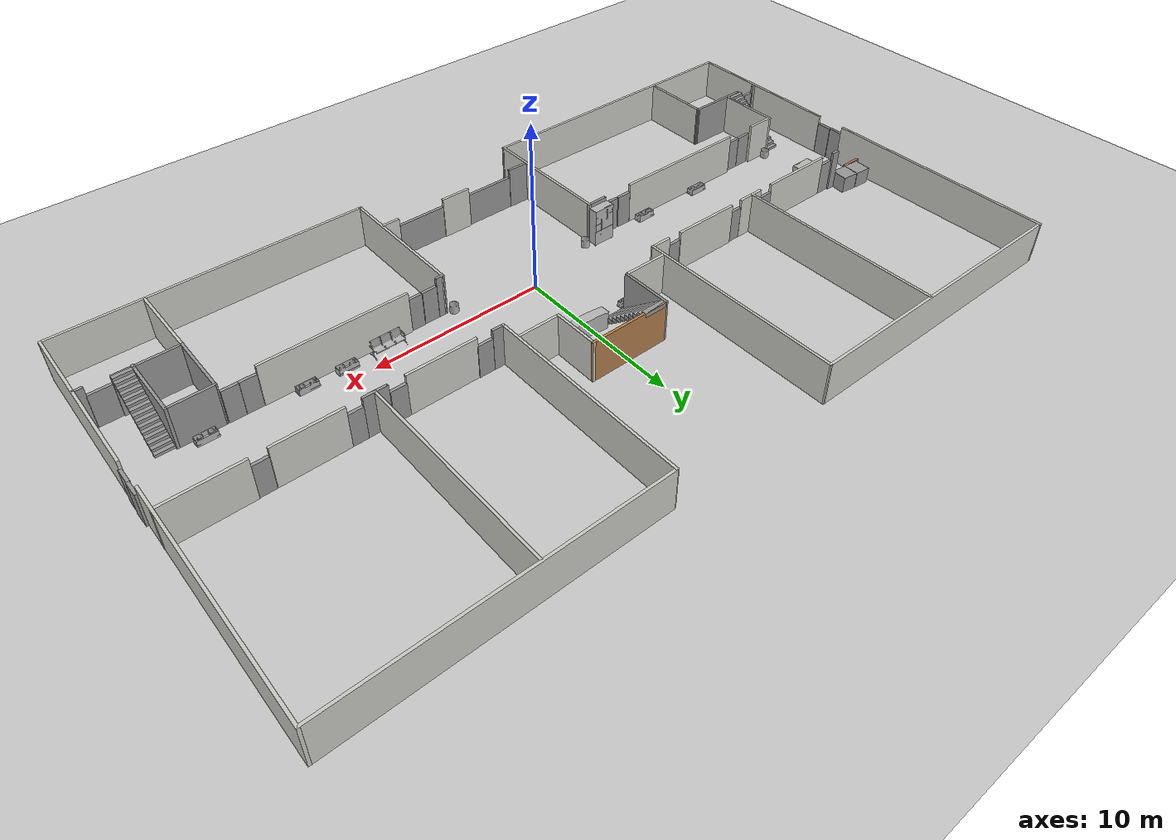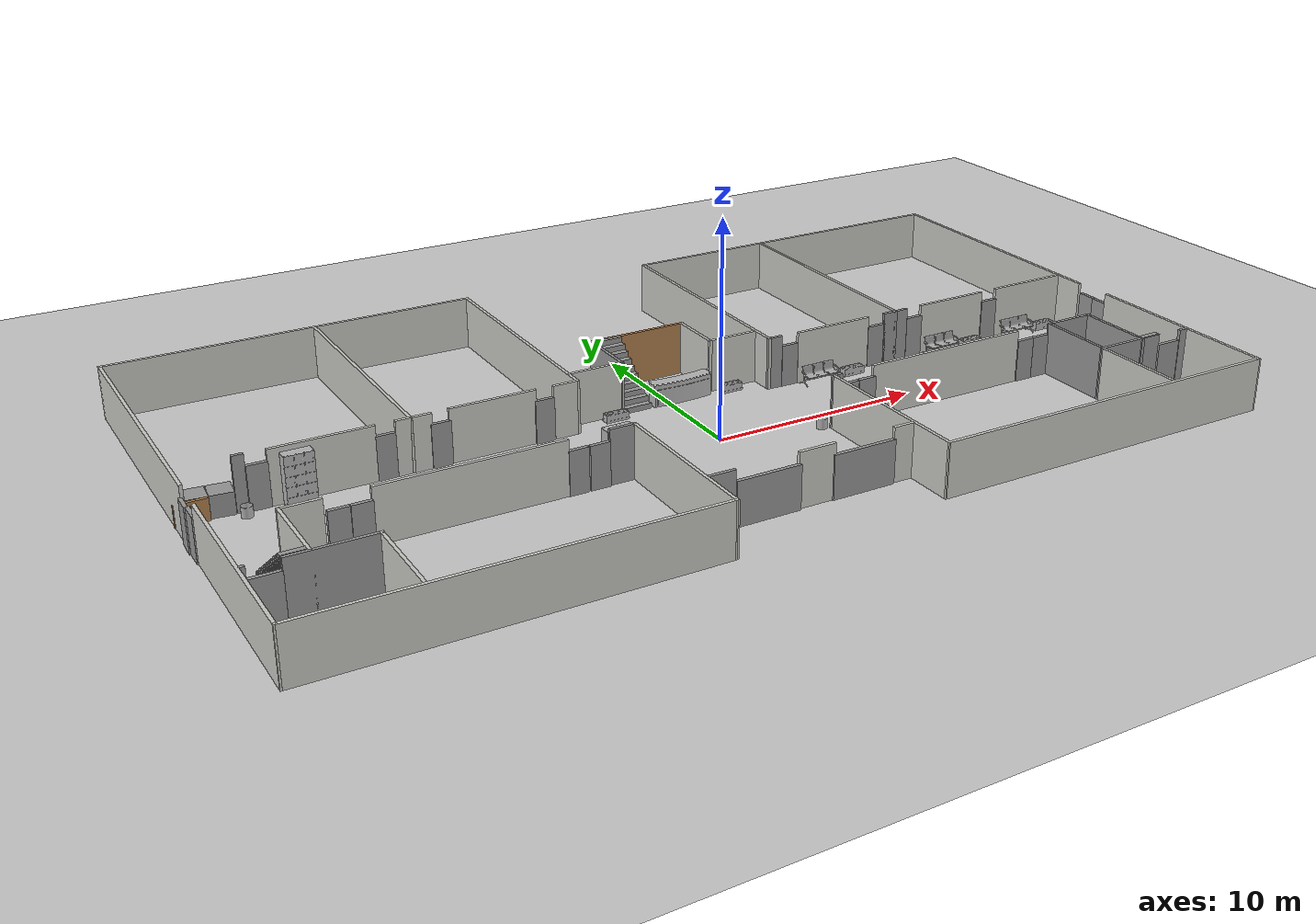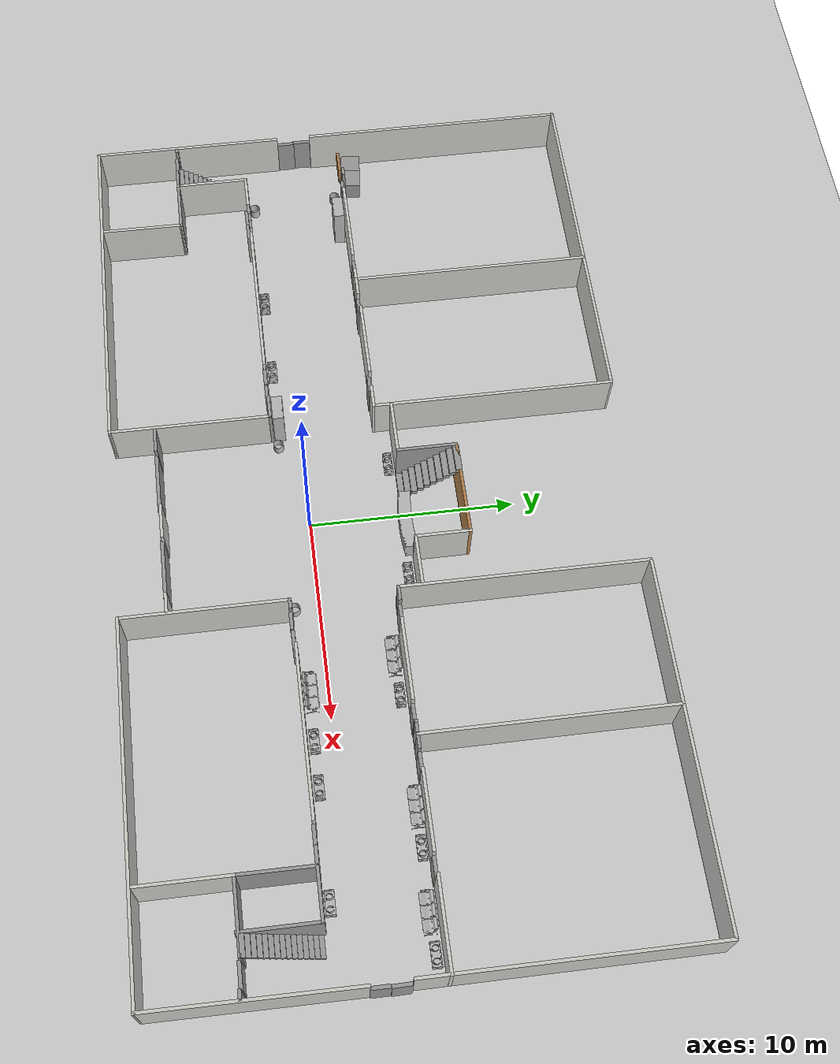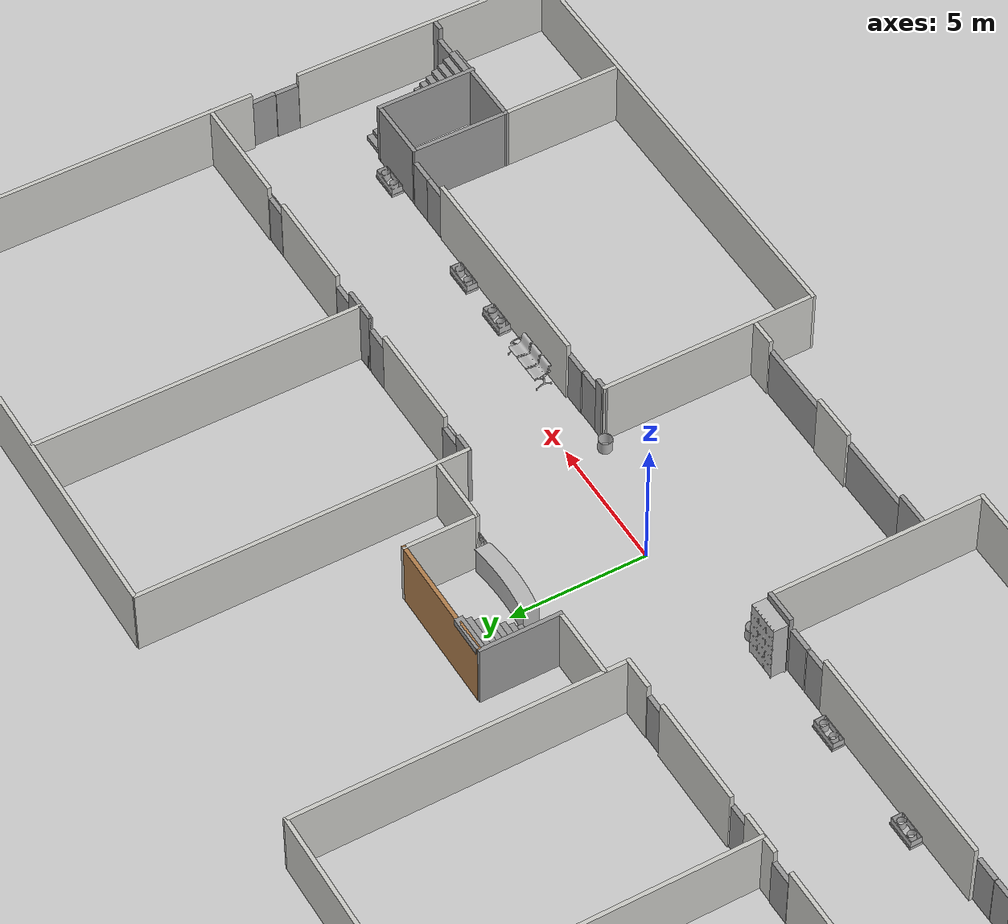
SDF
<sdf version="1.7">
 <world name="default">
  <light name="sun" type="directional">
   <pose>0 0 10 0 -0 0</pose>
   <diffuse>0.8 0.8 0.8 1</diffuse>
   <specular>0.2 0.2 0.2 1</specular>
   <attenuation>
    <range>1000</range>
    <constant>0.9</constant>
    <linear>0.01</linear>
    <quadratic>0.001</quadratic>
   </attenuation>
   <direction>-0.5 0.1 -0.9</direction>
   <spot><inner_angle>0</inner_angle><outer_angle>0</outer_angle><falloff>0</falloff></spot>
  </light>
  <model name="ground_plane">
   <static>1</static>
   <link name="link">
    <collision name="collision">
     <geometry><plane><normal>0 0 1</normal><size>100 100</size></plane></geometry>
     <surface><friction><ode><mu>100</mu><mu2>50</mu2></ode></friction></surface>
    </collision>
    <visual name="visual">
     <cast_shadows>0</cast_shadows>
     <geometry><plane><normal>0 0 1</normal><size>100 100</size></plane></geometry>
     <material>
      <script><uri>file://media/materials/scripts/gazebo.material</uri><name>Gazebo/Grey</name></script>
     </material>
    </visual>
   </link>
  </model>
  <gravity>0 0 -9.8</gravity>
  <magnetic_field>6e-06 2.3e-05 -4.2e-05</magnetic_field>
  <atmosphere type="adiabatic"/>
  <physics type="ode">
   <max_step_size>0.001</max_step_size>
   <real_time_factor>1</real_time_factor>
   <real_time_update_rate>1000</real_time_update_rate>
  </physics>
  <scene><ambient>0.4 0.4 0.4 1</ambient><background>0.7 0.7 0.7 1</background><shadows>0</shadows></scene>
  <audio><device>default</device></audio>
  <spherical_coordinates>
   <surface_model>EARTH_WGS84</surface_model>
   <latitude_deg>0</latitude_deg>
   <longitude_deg>0</longitude_deg>
   <elevation>0</elevation>
   <heading_deg>0</heading_deg>
  </spherical_coordinates>
  <model name="mts_dept">
   <pose>-0.0371 3.18794 0 0 -0 0</pose>
   <link name="Door_1">
    <collision name="Door_1_Collision">
     <geometry><box><size>0.9 0.17 2</size></box></geometry>
     <pose>0 0 1 0 -0 0</pose>
    </collision>
    <visual name="Door_1_Visual">
     <pose>0 0 1 0 -0 0</pose>
     <geometry><box><size>0.9 0.17 2</size></box></geometry>
     <material>
      <script><uri>file://media/materials/scripts/gazebo.material</uri><name>Gazebo/Grey</name></script>
     </material>
    </visual>
    <pose>-6.58213 -4.65147 0 0 -0 0</pose>
   </link>
   <link name="Door_13">
    <collision name="Door_13_Collision">
     <geometry><box><size>0.9 0.17 2</size></box></geometry>
     <pose>0 0 1 0 -0 0</pose>
    </collision>
    <visual name="Door_13_Visual">
     <pose>0 0 1 0 -0 0</pose>
     <geometry><box><size>0.9 0.17 2</size></box></geometry>
     <material>
      <script><uri>file://media/materials/scripts/gazebo.material</uri><name>Gazebo/Grey</name></script>
     </material>
    </visual>
    <pose>-22.3834 -2.29202 0 0 -0 -1.5708</pose>
   </link>
   <link name="Door_14">
    <collision name="Door_14_Collision">
     <geometry><box><size>0.9 0.17 2</size></box></geometry>
     <pose>0 0 1 0 -0 0</pose>
    </collision>
    <visual name="Door_14_Visual">
     <pose>0 0 1 0 -0 0</pose>
     <geometry><box><size>0.9 0.17 2</size></box></geometry>
     <material>
      <script><uri>file://media/materials/scripts/gazebo.material</uri><name>Gazebo/Grey</name></script>
     </material>
    </visual>
    <pose>-22.4286 -1.43294 0 0 0 -1.59865</pose>
   </link>
   <link name="Door_15">
    <collision name="Door_15_Collision">
     <geometry><box><size>1.25 0.17 2</size></box></geometry>
     <pose>0 0 1 0 -0 0</pose>
    </collision>
    <visual name="Door_15_Visual">
     <pose>0 0 1 0 -0 0</pose>
     <geometry><box><size>1.25 0.17 2</size></box></geometry>
     <material>
      <script><uri>file://media/materials/scripts/gazebo.material</uri><name>Gazebo/Grey</name></script>
     </material>
    </visual>
    <pose>21.2511 -8.1066 0 0 -0 0</pose>
   </link>
   <link name="Door_16">
    <collision name="Door_16_Collision">
     <geometry><box><size>0.9 0.17 2</size></box></geometry>
     <pose>0 0 1 0 -0 0</pose>
    </collision>
    <visual name="Door_16_Visual">
     <pose>0 0 1 0 -0 0</pose>
     <geometry><box><size>0.9 0.17 2</size></box></geometry>
     <material>
      <script><uri>file://media/materials/scripts/gazebo.material</uri><name>Gazebo/Grey</name></script>
     </material>
    </visual>
    <pose>16.6903 -4.48944 0 0 -0 0</pose>
   </link>
   <link name="Door_17">
    <collision name="Door_17_Collision">
     <geometry><box><size>0.9 0.17 2</size></box></geometry>
     <pose>0 0 1 0 -0 0</pose>
    </collision>
    <visual name="Door_17_Visual">
     <pose>0 0 1 0 -0 0</pose>
     <geometry><box><size>0.9 0.17 2</size></box></geometry>
     <material>
      <script><uri>file://media/materials/scripts/gazebo.material</uri><name>Gazebo/Grey</name></script>
     </material>
    </visual>
    <pose>15.7856 -4.48922 0 0 -0 0</pose>
   </link>
   <link name="Door_18">
    <collision name="Door_18_Collision">
     <geometry><box><size>0.9 0.17 2</size></box></geometry>
     <pose>0 0 1 0 -0 0</pose>
    </collision>
    <visual name="Door_18_Visual">
     <pose>0 0 1 0 -0 0</pose>
     <geometry><box><size>0.9 0.17 2</size></box></geometry>
     <material>
      <script><uri>file://media/materials/scripts/gazebo.material</uri><name>Gazebo/Grey</name></script>
     </material>
    </visual>
    <pose>5.7737 -4.55958 0 0 -0 0</pose>
   </link>
   <link name="Door_19">
    <collision name="Door_19_Collision">
     <geometry><box><size>0.9 0.17 2</size></box></geometry>
     <pose>0 0 1 0 -0 0</pose>
    </collision>
    <visual name="Door_19_Visual">
     <pose>0 0 1 0 -0 0</pose>
     <geometry><box><size>0.9 0.17 2</size></box></geometry>
     <material>
      <script><uri>file://media/materials/scripts/gazebo.material</uri><name>Gazebo/Grey</name></script>
     </material>
    </visual>
    <pose>6.71198 -4.54003 0 0 -0 0</pose>
   </link>
   <link name="Door_2">
    <collision name="Door_2_Collision">
     <geometry><box><size>0.9 0.17 2</size></box></geometry>
     <pose>0 0 1 0 -0 0</pose>
    </collision>
    <visual name="Door_2_Visual">
     <pose>0 0 1 0 -0 0</pose>
     <geometry><box><size>0.9 0.17 2</size></box></geometry>
     <material>
      <script><uri>file://media/materials/scripts/gazebo.material</uri><name>Gazebo/Grey</name></script>
     </material>
    </visual>
    <pose>-7.54552 -4.6498 0 0 -0 0</pose>
   </link>
   <link name="Door_20">
    <collision name="Door_20_Collision">
     <geometry><box><size>3 0.17 2</size></box></geometry>
     <pose>0 0 1 0 -0 0</pose>
    </collision>
    <visual name="Door_20_Visual">
     <pose>0 0 1 0 -0 0</pose>
     <geometry><box><size>3 0.17 2</size></box></geometry>
     <material>
      <script><uri>file://media/materials/scripts/gazebo.material</uri><name>Gazebo/Grey</name></script>
     </material>
    </visual>
    <pose>-2.13617 -10.29 0 0 -0 0</pose>
   </link>
   <link name="Door_21">
    <collision name="Door_21_Collision">
     <geometry><box><size>3 0.17 2</size></box></geometry>
     <pose>0 0 1 0 -0 0</pose>
    </collision>
    <visual name="Door_21_Visual">
     <pose>0 0 1 0 -0 0</pose>
     <geometry><box><size>3 0.17 2</size></box></geometry>
     <material>
      <script><uri>file://media/materials/scripts/gazebo.material</uri><name>Gazebo/Grey</name></script>
     </material>
    </visual>
    <pose>2.44244 -10.26 0 0 -0 0</pose>
   </link>
   <link name="Door_24">
    <collision name="Door_24_Collision">
     <geometry><box><size>0.9 0.17 2</size></box></geometry>
     <pose>0 0 1 0 -0 0</pose>
    </collision>
    <visual name="Door_24_Visual">
     <pose>0 0 1 0 -0 0</pose>
     <geometry><box><size>0.9 0.17 2</size></box></geometry>
     <material>
      <script><uri>file://media/materials/scripts/gazebo.material</uri><name>Gazebo/Grey</name></script>
     </material>
    </visual>
    <pose>13.1152 0.479726 0 0 -0 0</pose>
   </link>
   <link name="Door_25">
    <collision name="Door_25_Collision">
     <geometry><box><size>0.9 0.17 2</size></box></geometry>
     <pose>0 0 1 0 -0 0</pose>
    </collision>
    <visual name="Door_25_Visual">
     <pose>0 0 1 0 -0 0</pose>
     <geometry><box><size>0.9 0.17 2</size></box></geometry>
     <material>
      <script><uri>file://media/materials/scripts/gazebo.material</uri><name>Gazebo/Grey</name></script>
     </material>
    </visual>
    <pose>10.8334 0.469069 0 0 -0 0</pose>
   </link>
   <link name="Door_26">
    <collision name="Door_26_Collision">
     <geometry><box><size>0.9 0.17 2</size></box></geometry>
     <pose>0 0 1 0 -0 0</pose>
    </collision>
    <visual name="Door_26_Visual">
     <pose>0 0 1 0 -0 0</pose>
     <geometry><box><size>0.9 0.17 2</size></box></geometry>
     <material>
      <script><uri>file://media/materials/scripts/gazebo.material</uri><name>Gazebo/Grey</name></script>
     </material>
    </visual>
    <pose>5.99959 0.502503 0 0 -0 0</pose>
   </link>
   <link name="Door_27">
    <collision name="Door_27_Collision">
     <geometry><box><size>0.9 0.17 2</size></box></geometry>
     <pose>0 0 1 0 -0 0</pose>
    </collision>
    <visual name="Door_27_Visual">
     <pose>0 0 1 0 -0 0</pose>
     <geometry><box><size>0.9 0.17 2</size></box></geometry>
     <material>
      <script><uri>file://media/materials/scripts/gazebo.material</uri><name>Gazebo/Grey</name></script>
     </material>
    </visual>
    <pose>17.7287 0.488148 0 0 -0 0</pose>
   </link>
   <link name="Door_28">
    <collision name="Door_28_Collision">
     <geometry><box><size>0.9 0.17 2</size></box></geometry>
     <pose>0 0 1 0 -0 0</pose>
    </collision>
    <visual name="Door_28_Visual">
     <pose>0 0 1 0 -0 0</pose>
     <geometry><box><size>0.9 0.17 2</size></box></geometry>
     <material>
      <script><uri>file://media/materials/scripts/gazebo.material</uri><name>Gazebo/Grey</name></script>
     </material>
    </visual>
    <pose>22.4147 -1.51478 0 0 -0 1.58982</pose>
   </link>
   <link name="Door_29">
    <collision name="Door_29_Collision">
     <geometry><box><size>0.9 0.17 2</size></box></geometry>
     <pose>0 0 1 0 -0 0</pose>
    </collision>
    <visual name="Door_29_Visual">
     <pose>0 0 1 0 -0 0</pose>
     <geometry><box><size>0.9 0.17 2</size></box></geometry>
     <material>
      <script><uri>file://media/materials/scripts/gazebo.material</uri><name>Gazebo/Grey</name></script>
     </material>
    </visual>
    <pose>22.3942 -2.40723 0 0 -0 1.5708</pose>
   </link>
   <link name="Door_3">
    <collision name="Door_3_Collision">
     <geometry><box><size>0.9 0.17 2</size></box></geometry>
     <pose>0 0 1 0 -0 0</pose>
    </collision>
    <visual name="Door_3_Visual">
     <pose>0 0 1 0 -0 0</pose>
     <geometry><box><size>0.9 0.17 2</size></box></geometry>
     <material>
      <script><uri>file://media/materials/scripts/gazebo.material</uri><name>Gazebo/Grey</name></script>
     </material>
    </visual>
    <pose>-16.6533 -4.77247 0 0 -0 0</pose>
   </link>
   <link name="Door_4">
    <collision name="Door_4_Collision">
     <geometry><box><size>0.9 0.17 2</size></box></geometry>
     <pose>0 0 1 0 -0 0</pose>
    </collision>
    <visual name="Door_4_Visual">
     <pose>0 0 1 0 -0 0</pose>
     <geometry><box><size>0.9 0.17 2</size></box></geometry>
     <material>
      <script><uri>file://media/materials/scripts/gazebo.material</uri><name>Gazebo/Grey</name></script>
     </material>
    </visual>
    <pose>-17.5712 -4.7776 0 0 -0 0</pose>
   </link>
   <link name="Door_5">
    <collision name="Door_5_Collision">
     <geometry><box><size>1.25 0.17 2</size></box></geometry>
     <pose>0 0 1 0 -0 0</pose>
    </collision>
    <visual name="Door_5_Visual">
     <pose>0 0 1 0 -0 0</pose>
     <geometry><box><size>1.25 0.17 2</size></box></geometry>
     <material>
      <script><uri>file://media/materials/scripts/gazebo.material</uri><name>Gazebo/Grey</name></script>
     </material>
    </visual>
    <pose>-21.413 -8.25478 0 0 -0 0</pose>
   </link>
   <link name="Door_6">
    <collision name="Door_6_Collision">
     <geometry><box><size>0.9 0.17 2</size></box></geometry>
     <pose>0 0 1 0 -0 0</pose>
    </collision>
    <visual name="Door_6_Visual">
     <pose>0 0 1 0 -0 0</pose>
     <geometry><box><size>0.9 0.17 2</size></box></geometry>
     <material>
      <script><uri>file://media/materials/scripts/gazebo.material</uri><name>Gazebo/Grey</name></script>
     </material>
    </visual>
    <pose>-6.55285 0.494639 0 0 -0 0</pose>
   </link>
   <link name="Door_7">
    <collision name="Door_7_Collision">
     <geometry><box><size>0.9 0.17 2</size></box></geometry>
     <pose>0 0 1 0 -0 0</pose>
    </collision>
    <visual name="Door_7_Visual">
     <pose>0 0 1 0 -0 0</pose>
     <geometry><box><size>0.9 0.17 2</size></box></geometry>
     <material>
      <script><uri>file://media/materials/scripts/gazebo.material</uri><name>Gazebo/Grey</name></script>
     </material>
    </visual>
    <pose>-11.3046 0.493458 0 0 -0 0</pose>
   </link>
   <link name="Door_8">
    <collision name="Door_8_Collision">
     <geometry><box><size>0.9 0.17 2</size></box></geometry>
     <pose>0 0 1 0 -0 0</pose>
    </collision>
    <visual name="Door_8_Visual">
     <pose>0 0 1 0 -0 0</pose>
     <geometry><box><size>0.9 0.17 2</size></box></geometry>
     <material>
      <script><uri>file://media/materials/scripts/gazebo.material</uri><name>Gazebo/Grey</name></script>
     </material>
    </visual>
    <pose>-13.6938 0.528828 0 0 -0 0</pose>
   </link>
   <link name="Door_9">
    <collision name="Door_9_Collision">
     <geometry><box><size>0.9 0.17 2</size></box></geometry>
     <pose>0 0 1 0 -0 0</pose>
    </collision>
    <visual name="Door_9_Visual">
     <pose>0 0 1 0 -0 0</pose>
     <geometry><box><size>0.9 0.17 2</size></box></geometry>
     <material>
      <script><uri>file://media/materials/scripts/gazebo.material</uri><name>Gazebo/Grey</name></script>
     </material>
    </visual>
    <pose>-19.0487 0.509221 0 0 -0 0</pose>
   </link>
   <link name="Stairs_0">
    <visual name="Stairs_0_Visual_0">
     <pose>-20.3275 -4.74708 0.083333 0 -0 0</pose>
     <geometry><box><size>1 0.233333 0.166667</size></box></geometry>
     <material>
      <script><uri>file://media/materials/scripts/gazebo.material</uri><name>Gazebo/Grey</name></script>
      <ambient>1 1 1 1</ambient>
     </material>
     <meta><layer>0</layer></meta>
    </visual>
    <collision name="Stairs_0_Collision_0">
     <geometry><box><size>1 0.233333 0.166667</size></box></geometry>
     <pose>-20.3275 -4.74708 0.083333 0 -0 0</pose>
    </collision>
    <visual name="Stairs_0_Visual_1">
     <pose>-20.3275 -4.98041 0.25 0 -0 0</pose>
     <geometry><box><size>1 0.233333 0.166667</size></box></geometry>
     <material>
      <script><uri>file://media/materials/scripts/gazebo.material</uri><name>Gazebo/Grey</name></script>
      <ambient>1 1 1 1</ambient>
     </material>
     <meta><layer>0</layer></meta>
    </visual>
    <collision name="Stairs_0_Collision_1">
     <geometry><box><size>1 0.233333 0.166667</size></box></geometry>
     <pose>-20.3275 -4.98041 0.25 0 -0 0</pose>
    </collision>
    <visual name="Stairs_0_Visual_2">
     <pose>-20.3275 -5.21374 0.416667 0 -0 0</pose>
     <geometry><box><size>1 0.233333 0.166667</size></box></geometry>
     <material>
      <script><uri>file://media/materials/scripts/gazebo.material</uri><name>Gazebo/Grey</name></script>
      <ambient>1 1 1 1</ambient>
     </material>
     <meta><layer>0</layer></meta>
    </visual>
    <collision name="Stairs_0_Collision_2">
     <geometry><box><size>1 0.233333 0.166667</size></box></geometry>
     <pose>-20.3275 -5.21374 0.416667 0 -0 0</pose>
    </collision>
    <visual name="Stairs_0_Visual_3">
     <pose>-20.3275 -5.44708 0.583333 0 -0 0</pose>
     <geometry><box><size>1 0.233333 0.166667</size></box></geometry>
     <material>
      <script><uri>file://media/materials/scripts/gazebo.material</uri><name>Gazebo/Grey</name></script>
      <ambient>1 1 1 1</ambient>
     </material>
     <meta><layer>0</layer></meta>
    </visual>
    <collision name="Stairs_0_Collision_3">
     <geometry><box><size>1 0.233333 0.166667</size></box></geometry>
     <pose>-20.3275 -5.44708 0.583333 0 -0 0</pose>
    </collision>
    <visual name="Stairs_0_Visual_4">
     <pose>-20.3275 -5.68041 0.75 0 -0 0</pose>
     <geometry><box><size>1 0.233333 0.166667</size></box></geometry>
     <material>
      <script><uri>file://media/materials/scripts/gazebo.material</uri><name>Gazebo/Grey</name></script>
      <ambient>1 1 1 1</ambient>
     </material>
     <meta><layer>0</layer></meta>
    </visual>
    <collision name="Stairs_0_Collision_4">
     <geometry><box><size>1 0.233333 0.166667</size></box></geometry>
     <pose>-20.3275 -5.68041 0.75 0 -0 0</pose>
    </collision>
    <visual name="Stairs_0_Visual_5">
     <pose>-20.3275 -5.91374 0.916667 0 -0 0</pose>
     <geometry><box><size>1 0.233333 0.166667</size></box></geometry>
     <material>
      <script><uri>file://media/materials/scripts/gazebo.material</uri><name>Gazebo/Grey</name></script>
      <ambient>1 1 1 1</ambient>
     </material>
     <meta><layer>0</layer></meta>
    </visual>
    <collision name="Stairs_0_Collision_5">
     <geometry><box><size>1 0.233333 0.166667</size></box></geometry>
     <pose>-20.3275 -5.91374 0.916667 0 -0 0</pose>
    </collision>
    <visual name="Stairs_0_Visual_6">
     <pose>-20.3275 -6.14708 1.08333 0 -0 0</pose>
     <geometry><box><size>1 0.233333 0.166667</size></box></geometry>
     <material>
      <script><uri>file://media/materials/scripts/gazebo.material</uri><name>Gazebo/Grey</name></script>
      <ambient>1 1 1 1</ambient>
     </material>
     <meta><layer>0</layer></meta>
    </visual>
    <collision name="Stairs_0_Collision_6">
     <geometry><box><size>1 0.233333 0.166667</size></box></geometry>
     <pose>-20.3275 -6.14708 1.08333 0 -0 0</pose>
    </collision>
    <visual name="Stairs_0_Visual_7">
     <pose>-20.3275 -6.38041 1.25 0 -0 0</pose>
     <geometry><box><size>1 0.233333 0.166667</size></box></geometry>
     <material>
      <script><uri>file://media/materials/scripts/gazebo.material</uri><name>Gazebo/Grey</name></script>
      <ambient>1 1 1 1</ambient>
     </material>
     <meta><layer>0</layer></meta>
    </visual>
    <collision name="Stairs_0_Collision_7">
     <geometry><box><size>1 0.233333 0.166667</size></box></geometry>
     <pose>-20.3275 -6.38041 1.25 0 -0 0</pose>
    </collision>
    <visual name="Stairs_0_Visual_8">
     <pose>-20.3275 -6.61374 1.41667 0 -0 0</pose>
     <geometry><box><size>1 0.233333 0.166667</size></box></geometry>
     <material>
      <script><uri>file://media/materials/scripts/gazebo.material</uri><name>Gazebo/Grey</name></script>
      <ambient>1 1 1 1</ambient>
     </material>
     <meta><layer>0</layer></meta>
    </visual>
    <collision name="Stairs_0_Collision_8">
     <geometry><box><size>1 0.233333 0.166667</size></box></geometry>
     <pose>-20.3275 -6.61374 1.41667 0 -0 0</pose>
    </collision>
    <visual name="Stairs_0_Visual_9">
     <pose>-20.3275 -6.84708 1.58333 0 -0 0</pose>
     <geometry><box><size>1 0.233333 0.166667</size></box></geometry>
     <material>
      <script><uri>file://media/materials/scripts/gazebo.material</uri><name>Gazebo/Grey</name></script>
      <ambient>1 1 1 1</ambient>
     </material>
     <meta><layer>0</layer></meta>
    </visual>
    <collision name="Stairs_0_Collision_9">
     <geometry><box><size>1 0.233333 0.166667</size></box></geometry>
     <pose>-20.3275 -6.84708 1.58333 0 -0 0</pose>
    </collision>
    <visual name="Stairs_0_Visual_10">
     <pose>-20.3275 -7.08041 1.75 0 -0 0</pose>
     <geometry><box><size>1 0.233333 0.166667</size></box></geometry>
     <material>
      <script><uri>file://media/materials/scripts/gazebo.material</uri><name>Gazebo/Grey</name></script>
      <ambient>1 1 1 1</ambient>
     </material>
     <meta><layer>0</layer></meta>
    </visual>
    <collision name="Stairs_0_Collision_10">
     <geometry><box><size>1 0.233333 0.166667</size></box></geometry>
     <pose>-20.3275 -7.08041 1.75 0 -0 0</pose>
    </collision>
    <visual name="Stairs_0_Visual_11">
     <pose>-20.3275 -7.31374 1.91667 0 -0 0</pose>
     <geometry><box><size>1 0.233333 0.166667</size></box></geometry>
     <material>
      <script><uri>file://media/materials/scripts/gazebo.material</uri><name>Gazebo/Grey</name></script>
      <ambient>1 1 1 1</ambient>
     </material>
     <meta><layer>0</layer></meta>
    </visual>
    <collision name="Stairs_0_Collision_11">
     <geometry><box><size>1 0.233333 0.166667</size></box></geometry>
     <pose>-20.3275 -7.31374 1.91667 0 -0 0</pose>
    </collision>
    <visual name="Stairs_0_Visual_12">
     <pose>-20.3275 -7.54708 2.08333 0 -0 0</pose>
     <geometry><box><size>1 0.233333 0.166667</size></box></geometry>
     <material>
      <script><uri>file://media/materials/scripts/gazebo.material</uri><name>Gazebo/Grey</name></script>
      <ambient>1 1 1 1</ambient>
     </material>
     <meta><layer>0</layer></meta>
    </visual>
    <collision name="Stairs_0_Collision_12">
     <geometry><box><size>1 0.233333 0.166667</size></box></geometry>
     <pose>-20.3275 -7.54708 2.08333 0 -0 0</pose>
    </collision>
    <visual name="Stairs_0_Visual_13">
     <pose>-20.3275 -7.78041 2.25 0 -0 0</pose>
     <geometry><box><size>1 0.233333 0.166667</size></box></geometry>
     <material>
      <script><uri>file://media/materials/scripts/gazebo.material</uri><name>Gazebo/Grey</name></script>
      <ambient>1 1 1 1</ambient>
     </material>
     <meta><layer>0</layer></meta>
    </visual>
    <collision name="Stairs_0_Collision_13">
     <geometry><box><size>1 0.233333 0.166667</size></box></geometry>
     <pose>-20.3275 -7.78041 2.25 0 -0 0</pose>
    </collision>
    <visual name="Stairs_0_Visual_14">
     <pose>-20.3275 -8.01374 2.41667 0 -0 0</pose>
     <geometry><box><size>1 0.233333 0.166667</size></box></geometry>
     <material>
      <script><uri>file://media/materials/scripts/gazebo.material</uri><name>Gazebo/Grey</name></script>
      <ambient>1 1 1 1</ambient>
     </material>
     <meta><layer>0</layer></meta>
    </visual>
    <collision name="Stairs_0_Collision_14">
     <geometry><box><size>1 0.233333 0.166667</size></box></geometry>
     <pose>-20.3275 -8.01374 2.41667 0 -0 0</pose>
    </collision>
   </link>
   <link name="Stairs_2">
    <visual name="Stairs_2_Visual_0">
     <pose>20.1606 -4.63881 0.083333 0 -0 0</pose>
     <geometry><box><size>1 0.233333 0.166667</size></box></geometry>
     <material>
      <script><uri>file://media/materials/scripts/gazebo.material</uri><name>Gazebo/Grey</name></script>
      <ambient>1 1 1 1</ambient>
     </material>
     <meta><layer>0</layer></meta>
    </visual>
    <collision name="Stairs_2_Collision_0">
     <geometry><box><size>1 0.233333 0.166667</size></box></geometry>
     <pose>20.1606 -4.63881 0.083333 0 -0 0</pose>
    </collision>
    <visual name="Stairs_2_Visual_1">
     <pose>20.1606 -4.87214 0.25 0 -0 0</pose>
     <geometry><box><size>1 0.233333 0.166667</size></box></geometry>
     <material>
      <script><uri>file://media/materials/scripts/gazebo.material</uri><name>Gazebo/Grey</name></script>
      <ambient>1 1 1 1</ambient>
     </material>
     <meta><layer>0</layer></meta>
    </visual>
    <collision name="Stairs_2_Collision_1">
     <geometry><box><size>1 0.233333 0.166667</size></box></geometry>
     <pose>20.1606 -4.87214 0.25 0 -0 0</pose>
    </collision>
    <visual name="Stairs_2_Visual_2">
     <pose>20.1606 -5.10548 0.416667 0 -0 0</pose>
     <geometry><box><size>1 0.233333 0.166667</size></box></geometry>
     <material>
      <script><uri>file://media/materials/scripts/gazebo.material</uri><name>Gazebo/Grey</name></script>
      <ambient>1 1 1 1</ambient>
     </material>
     <meta><layer>0</layer></meta>
    </visual>
    <collision name="Stairs_2_Collision_2">
     <geometry><box><size>1 0.233333 0.166667</size></box></geometry>
     <pose>20.1606 -5.10548 0.416667 0 -0 0</pose>
    </collision>
    <visual name="Stairs_2_Visual_3">
     <pose>20.1606 -5.33881 0.583333 0 -0 0</pose>
     <geometry><box><size>1 0.233333 0.166667</size></box></geometry>
     <material>
      <script><uri>file://media/materials/scripts/gazebo.material</uri><name>Gazebo/Grey</name></script>
      <ambient>1 1 1 1</ambient>
     </material>
     <meta><layer>0</layer></meta>
    </visual>
    <collision name="Stairs_2_Collision_3">
     <geometry><box><size>1 0.233333 0.166667</size></box></geometry>
     <pose>20.1606 -5.33881 0.583333 0 -0 0</pose>
    </collision>
    <visual name="Stairs_2_Visual_4">
     <pose>20.1606 -5.57214 0.75 0 -0 0</pose>
     <geometry><box><size>1 0.233333 0.166667</size></box></geometry>
     <material>
      <script><uri>file://media/materials/scripts/gazebo.material</uri><name>Gazebo/Grey</name></script>
      <ambient>1 1 1 1</ambient>
     </material>
     <meta><layer>0</layer></meta>
    </visual>
    <collision name="Stairs_2_Collision_4">
     <geometry><box><size>1 0.233333 0.166667</size></box></geometry>
     <pose>20.1606 -5.57214 0.75 0 -0 0</pose>
    </collision>
    <visual name="Stairs_2_Visual_5">
     <pose>20.1606 -5.80548 0.916667 0 -0 0</pose>
     <geometry><box><size>1 0.233333 0.166667</size></box></geometry>
     <material>
      <script><uri>file://media/materials/scripts/gazebo.material</uri><name>Gazebo/Grey</name></script>
      <ambient>1 1 1 1</ambient>
     </material>
     <meta><layer>0</layer></meta>
    </visual>
    <collision name="Stairs_2_Collision_5">
     <geometry><box><size>1 0.233333 0.166667</size></box></geometry>
     <pose>20.1606 -5.80548 0.916667 0 -0 0</pose>
    </collision>
    <visual name="Stairs_2_Visual_6">
     <pose>20.1606 -6.03881 1.08333 0 -0 0</pose>
     <geometry><box><size>1 0.233333 0.166667</size></box></geometry>
     <material>
      <script><uri>file://media/materials/scripts/gazebo.material</uri><name>Gazebo/Grey</name></script>
      <ambient>1 1 1 1</ambient>
     </material>
     <meta><layer>0</layer></meta>
    </visual>
    <collision name="Stairs_2_Collision_6">
     <geometry><box><size>1 0.233333 0.166667</size></box></geometry>
     <pose>20.1606 -6.03881 1.08333 0 -0 0</pose>
    </collision>
    <visual name="Stairs_2_Visual_7">
     <pose>20.1606 -6.27214 1.25 0 -0 0</pose>
     <geometry><box><size>1 0.233333 0.166667</size></box></geometry>
     <material>
      <script><uri>file://media/materials/scripts/gazebo.material</uri><name>Gazebo/Grey</name></script>
      <ambient>1 1 1 1</ambient>
     </material>
     <meta><layer>0</layer></meta>
    </visual>
    <collision name="Stairs_2_Collision_7">
     <geometry><box><size>1 0.233333 0.166667</size></box></geometry>
     <pose>20.1606 -6.27214 1.25 0 -0 0</pose>
    </collision>
    <visual name="Stairs_2_Visual_8">
     <pose>20.1606 -6.50548 1.41667 0 -0 0</pose>
     <geometry><box><size>1 0.233333 0.166667</size></box></geometry>
     <material>
      <script><uri>file://media/materials/scripts/gazebo.material</uri><name>Gazebo/Grey</name></script>
      <ambient>1 1 1 1</ambient>
     </material>
     <meta><layer>0</layer></meta>
    </visual>
    <collision name="Stairs_2_Collision_8">
     <geometry><box><size>1 0.233333 0.166667</size></box></geometry>
     <pose>20.1606 -6.50548 1.41667 0 -0 0</pose>
    </collision>
    <visual name="Stairs_2_Visual_9">
     <pose>20.1606 -6.73881 1.58333 0 -0 0</pose>
     <geometry><box><size>1 0.233333 0.166667</size></box></geometry>
     <material>
      <script><uri>file://media/materials/scripts/gazebo.material</uri><name>Gazebo/Grey</name></script>
      <ambient>1 1 1 1</ambient>
     </material>
     <meta><layer>0</layer></meta>
    </visual>
    <collision name="Stairs_2_Collision_9">
     <geometry><box><size>1 0.233333 0.166667</size></box></geometry>
     <pose>20.1606 -6.73881 1.58333 0 -0 0</pose>
    </collision>
    <visual name="Stairs_2_Visual_10">
     <pose>20.1606 -6.97214 1.75 0 -0 0</pose>
     <geometry><box><size>1 0.233333 0.166667</size></box></geometry>
     <material>
      <script><uri>file://media/materials/scripts/gazebo.material</uri><name>Gazebo/Grey</name></script>
      <ambient>1 1 1 1</ambient>
     </material>
     <meta><layer>0</layer></meta>
    </visual>
    <collision name="Stairs_2_Collision_10">
     <geometry><box><size>1 0.233333 0.166667</size></box></geometry>
     <pose>20.1606 -6.97214 1.75 0 -0 0</pose>
    </collision>
    <visual name="Stairs_2_Visual_11">
     <pose>20.1606 -7.20548 1.91667 0 -0 0</pose>
     <geometry><box><size>1 0.233333 0.166667</size></box></geometry>
     <material>
      <script><uri>file://media/materials/scripts/gazebo.material</uri><name>Gazebo/Grey</name></script>
      <ambient>1 1 1 1</ambient>
     </material>
     <meta><layer>0</layer></meta>
    </visual>
    <collision name="Stairs_2_Collision_11">
     <geometry><box><size>1 0.233333 0.166667</size></box></geometry>
     <pose>20.1606 -7.20548 1.91667 0 -0 0</pose>
    </collision>
    <visual name="Stairs_2_Visual_12">
     <pose>20.1606 -7.43881 2.08333 0 -0 0</pose>
     <geometry><box><size>1 0.233333 0.166667</size></box></geometry>
     <material>
      <script><uri>file://media/materials/scripts/gazebo.material</uri><name>Gazebo/Grey</name></script>
      <ambient>1 1 1 1</ambient>
     </material>
     <meta><layer>0</layer></meta>
    </visual>
    <collision name="Stairs_2_Collision_12">
     <geometry><box><size>1 0.233333 0.166667</size></box></geometry>
     <pose>20.1606 -7.43881 2.08333 0 -0 0</pose>
    </collision>
    <visual name="Stairs_2_Visual_13">
     <pose>20.1606 -7.67214 2.25 0 -0 0</pose>
     <geometry><box><size>1 0.233333 0.166667</size></box></geometry>
     <material>
      <script><uri>file://media/materials/scripts/gazebo.material</uri><name>Gazebo/Grey</name></script>
      <ambient>1 1 1 1</ambient>
     </material>
     <meta><layer>0</layer></meta>
    </visual>
    <collision name="Stairs_2_Collision_13">
     <geometry><box><size>1 0.233333 0.166667</size></box></geometry>
     <pose>20.1606 -7.67214 2.25 0 -0 0</pose>
    </collision>
    <visual name="Stairs_2_Visual_14">
     <pose>20.1606 -7.90548 2.41667 0 -0 0</pose>
     <geometry><box><size>1 0.233333 0.166667</size></box></geometry>
     <material>
      <script><uri>file://media/materials/scripts/gazebo.material</uri><name>Gazebo/Grey</name></script>
      <ambient>1 1 1 1</ambient>
     </material>
     <meta><layer>0</layer></meta>
    </visual>
    <collision name="Stairs_2_Collision_14">
     <geometry><box><size>1 0.233333 0.166667</size></box></geometry>
     <pose>20.1606 -7.90548 2.41667 0 -0 0</pose>
    </collision>
   </link>
   <link name="Stairs_4">
    <visual name="Stairs_4_Visual_0">
     <pose>-1.55868 1.45214 0.125 0 0 -3.14159</pose>
     <geometry><box><size>1.36 0.304864 0.25</size></box></geometry>
     <material>
      <script><uri>file://media/materials/scripts/gazebo.material</uri><name>Gazebo/Grey</name></script>
      <ambient>0.368627 0.360784 0.392157 1</ambient>
     </material>
     <meta><layer>0</layer></meta>
    </visual>
    <collision name="Stairs_4_Collision_0">
     <geometry><box><size>1.36 0.304864 0.25</size></box></geometry>
     <pose>-1.55868 1.45214 0.125 0 0 -3.14159</pose>
    </collision>
    <visual name="Stairs_4_Visual_1">
     <pose>-1.55868 1.757 0.375 0 0 -3.14159</pose>
     <geometry><box><size>1.36 0.304864 0.25</size></box></geometry>
     <material>
      <script><uri>file://media/materials/scripts/gazebo.material</uri><name>Gazebo/Grey</name></script>
      <ambient>0.368627 0.360784 0.392157 1</ambient>
     </material>
     <meta><layer>0</layer></meta>
    </visual>
    <collision name="Stairs_4_Collision_1">
     <geometry><box><size>1.36 0.304864 0.25</size></box></geometry>
     <pose>-1.55868 1.757 0.375 0 0 -3.14159</pose>
    </collision>
    <visual name="Stairs_4_Visual_2">
     <pose>-1.55868 2.06187 0.625 0 0 -3.14159</pose>
     <geometry><box><size>1.36 0.304864 0.25</size></box></geometry>
     <material>
      <script><uri>file://media/materials/scripts/gazebo.material</uri><name>Gazebo/Grey</name></script>
      <ambient>0.368627 0.360784 0.392157 1</ambient>
     </material>
     <meta><layer>0</layer></meta>
    </visual>
    <collision name="Stairs_4_Collision_2">
     <geometry><box><size>1.36 0.304864 0.25</size></box></geometry>
     <pose>-1.55868 2.06187 0.625 0 0 -3.14159</pose>
    </collision>
    <visual name="Stairs_4_Visual_3">
     <pose>-1.55868 2.36673 0.875 0 0 -3.14159</pose>
     <geometry><box><size>1.36 0.304864 0.25</size></box></geometry>
     <material>
      <script><uri>file://media/materials/scripts/gazebo.material</uri><name>Gazebo/Grey</name></script>
      <ambient>0.368627 0.360784 0.392157 1</ambient>
     </material>
     <meta><layer>0</layer></meta>
    </visual>
    <collision name="Stairs_4_Collision_3">
     <geometry><box><size>1.36 0.304864 0.25</size></box></geometry>
     <pose>-1.55868 2.36673 0.875 0 0 -3.14159</pose>
    </collision>
    <visual name="Stairs_4_Visual_4">
     <pose>-1.55868 2.67159 1.125 0 0 -3.14159</pose>
     <geometry><box><size>1.36 0.304864 0.25</size></box></geometry>
     <material>
      <script><uri>file://media/materials/scripts/gazebo.material</uri><name>Gazebo/Grey</name></script>
      <ambient>0.368627 0.360784 0.392157 1</ambient>
     </material>
     <meta><layer>0</layer></meta>
    </visual>
    <collision name="Stairs_4_Collision_4">
     <geometry><box><size>1.36 0.304864 0.25</size></box></geometry>
     <pose>-1.55868 2.67159 1.125 0 0 -3.14159</pose>
    </collision>
    <visual name="Stairs_4_Visual_5">
     <pose>-1.55868 2.97646 1.375 0 0 -3.14159</pose>
     <geometry><box><size>1.36 0.304864 0.25</size></box></geometry>
     <material>
      <script><uri>file://media/materials/scripts/gazebo.material</uri><name>Gazebo/Grey</name></script>
      <ambient>0.368627 0.360784 0.392157 1</ambient>
     </material>
     <meta><layer>0</layer></meta>
    </visual>
    <collision name="Stairs_4_Collision_5">
     <geometry><box><size>1.36 0.304864 0.25</size></box></geometry>
     <pose>-1.55868 2.97646 1.375 0 0 -3.14159</pose>
    </collision>
    <visual name="Stairs_4_Visual_6">
     <pose>-1.55868 3.28132 1.625 0 0 -3.14159</pose>
     <geometry><box><size>1.36 0.304864 0.25</size></box></geometry>
     <material>
      <script><uri>file://media/materials/scripts/gazebo.material</uri><name>Gazebo/Grey</name></script>
      <ambient>0.368627 0.360784 0.392157 1</ambient>
     </material>
     <meta><layer>0</layer></meta>
    </visual>
    <collision name="Stairs_4_Collision_6">
     <geometry><box><size>1.36 0.304864 0.25</size></box></geometry>
     <pose>-1.55868 3.28132 1.625 0 0 -3.14159</pose>
    </collision>
    <visual name="Stairs_4_Visual_7">
     <pose>-1.55868 3.58619 1.875 0 0 -3.14159</pose>
     <geometry><box><size>1.36 0.304864 0.25</size></box></geometry>
     <material>
      <script><uri>file://media/materials/scripts/gazebo.material</uri><name>Gazebo/Grey</name></script>
      <ambient>0.368627 0.360784 0.392157 1</ambient>
     </material>
     <meta><layer>0</layer></meta>
    </visual>
    <collision name="Stairs_4_Collision_7">
     <geometry><box><size>1.36 0.304864 0.25</size></box></geometry>
     <pose>-1.55868 3.58619 1.875 0 0 -3.14159</pose>
    </collision>
    <visual name="Stairs_4_Visual_8">
     <pose>-1.55868 3.89105 2.125 0 0 -3.14159</pose>
     <geometry><box><size>1.36 0.304864 0.25</size></box></geometry>
     <material>
      <script><uri>file://media/materials/scripts/gazebo.material</uri><name>Gazebo/Grey</name></script>
      <ambient>0.368627 0.360784 0.392157 1</ambient>
     </material>
     <meta><layer>0</layer></meta>
    </visual>
    <collision name="Stairs_4_Collision_8">
     <geometry><box><size>1.36 0.304864 0.25</size></box></geometry>
     <pose>-1.55868 3.89105 2.125 0 0 -3.14159</pose>
    </collision>
    <visual name="Stairs_4_Visual_9">
     <pose>-1.55868 4.19592 2.375 0 0 -3.14159</pose>
     <geometry><box><size>1.36 0.304864 0.25</size></box></geometry>
     <material>
      <script><uri>file://media/materials/scripts/gazebo.material</uri><name>Gazebo/Grey</name></script>
      <ambient>0.368627 0.360784 0.392157 1</ambient>
     </material>
     <meta><layer>0</layer></meta>
    </visual>
    <collision name="Stairs_4_Collision_9">
     <geometry><box><size>1.36 0.304864 0.25</size></box></geometry>
     <pose>-1.55868 4.19592 2.375 0 0 -3.14159</pose>
    </collision>
   </link>
   <link name="Wall_104">
    <collision name="Wall_104_Collision">
     <geometry><box><size>13.5 0.15 2.5</size></box></geometry>
     <pose>0 0 1.25 0 -0 0</pose>
    </collision>
    <visual name="Wall_104_Visual">
     <pose>0 0 1.25 0 -0 0</pose>
     <geometry><box><size>13.5 0.15 2.5</size></box></geometry>
     <material>
      <script><uri>file://media/materials/scripts/gazebo.material</uri><name>Gazebo/CeilingTiled</name></script>
      <ambient>1 1 1 1</ambient>
     </material>
     <meta><layer>0</layer></meta>
    </visual>
    <pose>-22.3402 5.7797 0 0 -0 -1.5708</pose>
   </link>
   <link name="Wall_109">
    <collision name="Wall_109_Collision">
     <geometry><box><size>9.75 0.15 2.5</size></box></geometry>
     <pose>0 0 1.25 0 -0 0</pose>
    </collision>
    <visual name="Wall_109_Visual">
     <pose>0 0 1.25 0 -0 0</pose>
     <geometry><box><size>9.75 0.15 2.5</size></box></geometry>
     <material>
      <script><uri>file://media/materials/scripts/gazebo.material</uri><name>Gazebo/CeilingTiled</name></script>
      <ambient>1 1 1 1</ambient>
     </material>
     <meta><layer>0</layer></meta>
    </visual>
    <pose>-22.3402 -7.5953 0 0 -0 1.5708</pose>
   </link>
   <link name="Wall_111">
    <collision name="Wall_111_Collision">
     <geometry><box><size>3.5 0.15 2.5</size></box></geometry>
     <pose>0 0 1.25 0 -0 0</pose>
    </collision>
    <visual name="Wall_111_Visual">
     <pose>0 0 1.25 0 -0 0</pose>
     <geometry><box><size>3.5 0.15 2.5</size></box></geometry>
     <material>
      <script><uri>file://media/materials/scripts/gazebo.material</uri><name>Gazebo/Grey</name></script>
      <ambient>1 1 1 1</ambient>
     </material>
     <meta><layer>0</layer></meta>
    </visual>
    <pose>18.9077 -8.02797 0 0 -0 3.14159</pose>
   </link>
   <link name="Wall_112">
    <collision name="Wall_112_Collision">
     <geometry><box><size>4.5 0.15 2.5</size></box></geometry>
     <pose>0 0 1.25 0 -0 0</pose>
    </collision>
    <visual name="Wall_112_Visual">
     <pose>0 0 1.25 0 -0 0</pose>
     <geometry><box><size>4.5 0.15 2.5</size></box></geometry>
     <material>
      <script><uri>file://media/materials/scripts/gazebo.material</uri><name>Gazebo/CeilingTiled</name></script>
      <ambient>1 1 1 1</ambient>
     </material>
     <meta><layer>0</layer></meta>
    </visual>
    <pose>17.2327 -10.203 0 0 -0 -1.5708</pose>
   </link>
   <link name="Wall_114">
    <collision name="Wall_114_Collision">
     <geometry><box><size>0.5 0.15 2.5</size></box></geometry>
     <pose>0 0 1.25 0 -0 0</pose>
    </collision>
    <visual name="Wall_114_Visual">
     <pose>0 0 1.25 0 -0 0</pose>
     <geometry><box><size>0.5 0.15 2.5</size></box></geometry>
     <material>
      <script><uri>file://media/materials/scripts/gazebo.material</uri><name>Gazebo/Grey</name></script>
      <ambient>1 1 1 1</ambient>
     </material>
     <meta><layer>0</layer></meta>
    </visual>
    <pose>22.0983 -8.14592 0 0 -0 3.14159</pose>
   </link>
   <link name="Wall_116">
    <collision name="Wall_116_Collision">
     <geometry><box><size>2.5 0.15 2.5</size></box></geometry>
     <pose>0 0 1.25 0 -0 0</pose>
    </collision>
    <visual name="Wall_116_Visual">
     <pose>0 0 1.25 0 -0 0</pose>
     <geometry><box><size>2.5 0.15 2.5</size></box></geometry>
     <material>
      <script><uri>file://media/materials/scripts/gazebo.material</uri><name>Gazebo/Grey</name></script>
      <ambient>1 1 1 1</ambient>
     </material>
     <meta><layer>0</layer></meta>
    </visual>
    <pose>18.4248 -4.48944 0 0 -0 3.14159</pose>
   </link>
   <link name="Wall_117">
    <collision name="Wall_117_Collision">
     <geometry><box><size>3.68857 0.15 2.5</size></box></geometry>
     <pose>0 0 1.25 0 -0 0</pose>
    </collision>
    <visual name="Wall_117_Visual">
     <pose>0 0 1.25 0 -0 0</pose>
     <geometry><box><size>3.68857 0.15 2.5</size></box></geometry>
     <material>
      <script><uri>file://media/materials/scripts/gazebo.material</uri><name>Gazebo/Grey</name></script>
      <ambient>1 1 1 1</ambient>
     </material>
     <meta><layer>0</layer></meta>
    </visual>
    <pose>17.2412 -6.2587 0 0 -0 -1.57562</pose>
   </link>
   <link name="Wall_119">
    <collision name="Wall_119_Collision">
     <geometry><box><size>8.25 0.15 2.5</size></box></geometry>
     <pose>0 0 1.25 0 -0 0</pose>
    </collision>
    <visual name="Wall_119_Visual">
     <pose>0 0 1.25 0 -0 0</pose>
     <geometry><box><size>8.25 0.15 2.5</size></box></geometry>
     <material>
      <script><uri>file://media/materials/scripts/gazebo.material</uri><name>Gazebo/CeilingTiled</name></script>
      <ambient>1 1 1 1</ambient>
     </material>
     <meta><layer>0</layer></meta>
    </visual>
    <pose>11.192 -4.46184 0 0 -0 0</pose>
   </link>
   <link name="Wall_122">
    <collision name="Wall_122_Collision">
     <geometry><box><size>0.5 0.15 2.5</size></box></geometry>
     <pose>0 0 1.25 0 -0 0</pose>
    </collision>
    <visual name="Wall_122_Visual">
     <pose>0 0 1.25 0 -0 0</pose>
     <geometry><box><size>0.5 0.15 2.5</size></box></geometry>
     <material>
      <script><uri>file://media/materials/scripts/gazebo.material</uri><name>Gazebo/Grey</name></script>
      <ambient>1 1 1 1</ambient>
     </material>
     <meta><layer>0</layer></meta>
    </visual>
    <pose>5.10893 -4.53609 0 0 -0 0</pose>
   </link>
   <link name="Wall_124">
    <collision name="Wall_124_Collision">
     <geometry><box><size>3.75 0.15 2.5</size></box></geometry>
     <pose>0 0 1.25 0 -0 0</pose>
    </collision>
    <visual name="Wall_124_Visual">
     <pose>0 0 1.25 0 -0 0</pose>
     <geometry><box><size>3.75 0.15 2.5</size></box></geometry>
     <material>
      <script><uri>file://media/materials/scripts/gazebo.material</uri><name>Gazebo/CeilingTiled</name></script>
      <ambient>1 1 1 1</ambient>
     </material>
     <meta><layer>0</layer></meta>
    </visual>
    <pose>-19.7688 -6.45147 0 0 -0 -1.5708</pose>
   </link>
   <link name="Wall_126">
    <collision name="Wall_126_Collision">
     <geometry><box><size>3.75 0.15 2.5</size></box></geometry>
     <pose>0 0 1.25 0 -0 0</pose>
    </collision>
    <visual name="Wall_126_Visual">
     <pose>0 0 1.25 0 -0 0</pose>
     <geometry><box><size>3.75 0.15 2.5</size></box></geometry>
     <material>
      <script><uri>file://media/materials/scripts/gazebo.material</uri><name>Gazebo/Grey</name></script>
      <ambient>1 1 1 1</ambient>
     </material>
     <meta><layer>0</layer></meta>
    </visual>
    <pose>19.5998 -6.28944 0 0 -0 -1.5708</pose>
   </link>
   <link name="Wall_135">
    <collision name="Wall_135_Collision">
     <geometry><box><size>2.5 0.15 2.5</size></box></geometry>
     <pose>0 0 1.25 0 -0 0</pose>
    </collision>
    <visual name="Wall_135_Visual">
     <pose>0 0 1.25 0 -0 0</pose>
     <geometry><box><size>2.5 0.15 2.5</size></box></geometry>
     <material>
      <script><uri>file://media/materials/scripts/gazebo.material</uri><name>Gazebo/CeilingTiled</name></script>
      <ambient>1 1 1 1</ambient>
     </material>
     <meta><layer>0</layer></meta>
    </visual>
    <pose>3.56759 1.65434 0 0 -0 0</pose>
   </link>
   <link name="Wall_137">
    <collision name="Wall_137_Collision">
     <geometry><box><size>2.75 0.15 2.5</size></box></geometry>
     <pose>0 0 1.25 0 -0 0</pose>
    </collision>
    <visual name="Wall_137_Visual">
     <pose>0 0 1.25 0 -0 0</pose>
     <geometry><box><size>2.75 0.15 2.5</size></box></geometry>
     <material>
      <script><uri>file://media/materials/scripts/gazebo.material</uri><name>Gazebo/CeilingTiled</name></script>
      <ambient>1 1 1 1</ambient>
     </material>
     <meta><layer>0</layer></meta>
    </visual>
    <pose>2.39259 2.95433 0 0 -0 1.5708</pose>
   </link>
   <link name="Wall_138">
    <collision name="Wall_138_Collision">
     <geometry><box><size>4.75 0.15 2.5</size></box></geometry>
     <pose>0 0 1.25 0 -0 0</pose>
    </collision>
    <visual name="Wall_138_Visual">
     <pose>0 0 1.25 0 -0 0</pose>
     <geometry><box><size>4.75 0.15 2.5</size></box></geometry>
     <material>
      <script><uri>file://media/materials/scripts/gazebo.material</uri><name>Gazebo/Wood</name></script>
      <ambient>1 1 1 1</ambient>
     </material>
     <meta><layer>0</layer></meta>
    </visual>
    <pose>0.092593 4.25433 0 0 -0 3.14159</pose>
   </link>
   <link name="Wall_141">
    <collision name="Wall_141_Collision">
     <geometry><box><size>3 0.15 2.5</size></box></geometry>
     <pose>0 0 1.25 0 -0 0</pose>
    </collision>
    <visual name="Wall_141_Visual">
     <pose>0 0 1.25 0 -0 0</pose>
     <geometry><box><size>3 0.15 2.5</size></box></geometry>
     <material>
      <script><uri>file://media/materials/scripts/gazebo.material</uri><name>Gazebo/Grey</name></script>
      <ambient>1 1 1 1</ambient>
     </material>
     <meta><layer>0</layer></meta>
    </visual>
    <pose>-2.31448 2.81677 0 0 -0 1.5708</pose>
   </link>
   <link name="Wall_143">
    <collision name="Wall_143_Collision">
     <geometry><box><size>2.75 0.15 2.5</size></box></geometry>
     <pose>0 0 1.25 0 -0 0</pose>
    </collision>
    <visual name="Wall_143_Visual">
     <pose>0 0 1.25 0 -0 0</pose>
     <geometry><box><size>2.75 0.15 2.5</size></box></geometry>
     <material>
      <script><uri>file://media/materials/scripts/gazebo.material</uri><name>Gazebo/CeilingTiled</name></script>
      <ambient>1 1 1 1</ambient>
     </material>
     <meta><layer>0</layer></meta>
    </visual>
    <pose>-3.61449 1.39177 0 0 -0 0</pose>
   </link>
   <link name="Wall_145">
    <collision name="Wall_145_Collision">
     <geometry><box><size>1.75 0.15 2.5</size></box></geometry>
     <pose>0 0 1.25 0 -0 0</pose>
    </collision>
    <visual name="Wall_145_Visual">
     <pose>0 0 1.25 0 -0 0</pose>
     <geometry><box><size>1.75 0.15 2.5</size></box></geometry>
     <material>
      <script><uri>file://media/materials/scripts/gazebo.material</uri><name>Gazebo/CeilingTiled</name></script>
      <ambient>1 1 1 1</ambient>
     </material>
     <meta><layer>0</layer></meta>
    </visual>
    <pose>0.168158 -10.2005 0 0 -0 0</pose>
   </link>
   <link name="Wall_147">
    <collision name="Wall_147_Collision">
     <geometry><box><size>1 0.15 2.5</size></box></geometry>
     <pose>0 0 1.25 0 -0 0</pose>
    </collision>
    <visual name="Wall_147_Visual">
     <pose>0 0 1.25 0 -0 0</pose>
     <geometry><box><size>1 0.15 2.5</size></box></geometry>
     <material>
      <script><uri>file://media/materials/scripts/gazebo.material</uri><name>Gazebo/CeilingTiled</name></script>
      <ambient>1 1 1 1</ambient>
     </material>
     <meta><layer>0</layer></meta>
    </visual>
    <pose>4.41336 -10.2005 0 0 -0 0</pose>
   </link>
   <link name="Wall_149">
    <collision name="Wall_149_Collision">
     <geometry><box><size>1.25 0.15 2.5</size></box></geometry>
     <pose>0 0 1.25 0 -0 0</pose>
    </collision>
    <visual name="Wall_149_Visual">
     <pose>0 0 1.25 0 -0 0</pose>
     <geometry><box><size>1.25 0.15 2.5</size></box></geometry>
     <material>
      <script><uri>file://media/materials/scripts/gazebo.material</uri><name>Gazebo/Grey</name></script>
      <ambient>1 1 1 1</ambient>
     </material>
     <meta><layer>0</layer></meta>
    </visual>
    <pose>-4.26152 -10.26 0 0 -0 3.14159</pose>
   </link>
   <link name="Wall_151">
    <collision name="Wall_151_Collision">
     <geometry><box><size>12 0.15 2.5</size></box></geometry>
     <pose>0 0 1.25 0 -0 0</pose>
    </collision>
    <visual name="Wall_151_Visual">
     <pose>0 0 1.25 0 -0 0</pose>
     <geometry><box><size>12 0.15 2.5</size></box></geometry>
     <material>
      <script><uri>file://media/materials/scripts/gazebo.material</uri><name>Gazebo/CeilingTiled</name></script>
      <ambient>1 1 1 1</ambient>
     </material>
     <meta><layer>0</layer></meta>
    </visual>
    <pose>-12.6013 6.44232 0 0 -0 1.5708</pose>
   </link>
   <link name="Wall_153">
    <collision name="Wall_153_Collision">
     <geometry><box><size>4 0.15 2.5</size></box></geometry>
     <pose>0 0 1.25 0 -0 0</pose>
    </collision>
    <visual name="Wall_153_Visual">
     <pose>0 0 1.25 0 -0 0</pose>
     <geometry><box><size>4 0.15 2.5</size></box></geometry>
     <material>
      <script><uri>file://media/materials/scripts/gazebo.material</uri><name>Gazebo/CeilingTiled</name></script>
      <ambient>1 1 1 1</ambient>
     </material>
     <meta><layer>0</layer></meta>
    </visual>
    <pose>-8.91338 0.557706 0 0 -0 3.14159</pose>
   </link>
   <link name="Wall_155">
    <collision name="Wall_155_Collision">
     <geometry><box><size>1 0.15 2.5</size></box></geometry>
     <pose>0 0 1.25 0 -0 0</pose>
    </collision>
    <visual name="Wall_155_Visual">
     <pose>0 0 1.25 0 -0 0</pose>
     <geometry><box><size>1 0.15 2.5</size></box></geometry>
     <material>
      <script><uri>file://media/materials/scripts/gazebo.material</uri><name>Gazebo/CeilingTiled</name></script>
      <ambient>1 1 1 1</ambient>
     </material>
     <meta><layer>0</layer></meta>
    </visual>
    <pose>-12.1763 0.517323 0 0 -0 0</pose>
   </link>
   <link name="Wall_157">
    <collision name="Wall_157_Collision">
     <geometry><box><size>4.5 0.15 2.5</size></box></geometry>
     <pose>0 0 1.25 0 -0 0</pose>
    </collision>
    <visual name="Wall_157_Visual">
     <pose>0 0 1.25 0 -0 0</pose>
     <geometry><box><size>4.5 0.15 2.5</size></box></geometry>
     <material>
      <script><uri>file://media/materials/scripts/gazebo.material</uri><name>Gazebo/CeilingTiled</name></script>
      <ambient>1 1 1 1</ambient>
     </material>
     <meta><layer>0</layer></meta>
    </visual>
    <pose>-16.3742 0.519684 0 0 -0 0</pose>
   </link>
   <link name="Wall_160">
    <collision name="Wall_160_Collision">
     <geometry><box><size>0.75 0.15 2.5</size></box></geometry>
     <pose>0 0 1.25 0 -0 0</pose>
    </collision>
    <visual name="Wall_160_Visual">
     <pose>0 0 1.25 0 -0 0</pose>
     <geometry><box><size>0.75 0.15 2.5</size></box></geometry>
     <material>
      <script><uri>file://media/materials/scripts/gazebo.material</uri><name>Gazebo/CeilingTiled</name></script>
      <ambient>1 1 1 1</ambient>
     </material>
     <meta><layer>0</layer></meta>
    </visual>
    <pose>-12.9013 0.517323 0 0 -0 3.14159</pose>
   </link>
   <link name="Wall_166">
    <collision name="Wall_166_Collision">
     <geometry><box><size>0.5 0.15 2.5</size></box></geometry>
     <pose>0 0 1.25 0 -0 0</pose>
    </collision>
    <visual name="Wall_166_Visual">
     <pose>0 0 1.25 0 -0 0</pose>
     <geometry><box><size>0.5 0.15 2.5</size></box></geometry>
     <material>
      <script><uri>file://media/materials/scripts/gazebo.material</uri><name>Gazebo/Grey</name></script>
      <ambient>1 1 1 1</ambient>
     </material>
     <meta><layer>0</layer></meta>
    </visual>
    <pose>-19.7405 0.612956 0 0 -0 3.14159</pose>
   </link>
   <link name="Wall_170">
    <collision name="Wall_170_Collision">
     <geometry><box><size>12 0.15 2.5</size></box></geometry>
     <pose>0 0 1.25 0 -0 0</pose>
    </collision>
    <visual name="Wall_170_Visual">
     <pose>0 0 1.25 0 -0 0</pose>
     <geometry><box><size>12 0.15 2.5</size></box></geometry>
     <material>
      <script><uri>file://media/materials/scripts/gazebo.material</uri><name>Gazebo/CeilingTiled</name></script>
      <ambient>1 1 1 1</ambient>
     </material>
     <meta><layer>0</layer></meta>
    </visual>
    <pose>11.9938 6.40566 0 0 -0 1.5708</pose>
   </link>
   <link name="Wall_172">
    <collision name="Wall_172_Collision">
     <geometry><box><size>0.75 0.15 2.5</size></box></geometry>
     <pose>0 0 1.25 0 -0 0</pose>
    </collision>
    <visual name="Wall_172_Visual">
     <pose>0 0 1.25 0 -0 0</pose>
     <geometry><box><size>0.75 0.15 2.5</size></box></geometry>
     <material>
      <script><uri>file://media/materials/scripts/gazebo.material</uri><name>Gazebo/Grey</name></script>
      <ambient>1 1 1 1</ambient>
     </material>
     <meta><layer>0</layer></meta>
    </visual>
    <pose>5.17582 0.518761 0 0 -0 0</pose>
   </link>
   <link name="Wall_174">
    <collision name="Wall_174_Collision">
     <geometry><box><size>4 0.15 2.5</size></box></geometry>
     <pose>0 0 1.25 0 -0 0</pose>
    </collision>
    <visual name="Wall_174_Visual">
     <pose>0 0 1.25 0 -0 0</pose>
     <geometry><box><size>4 0.15 2.5</size></box></geometry>
     <material>
      <script><uri>file://media/materials/scripts/gazebo.material</uri><name>Gazebo/CeilingTiled</name></script>
      <ambient>1 1 1 1</ambient>
     </material>
     <meta><layer>0</layer></meta>
    </visual>
    <pose>8.40586 0.475907 0 0 -0 0</pose>
   </link>
   <link name="Wall_179">
    <collision name="Wall_179_Collision">
     <geometry><box><size>0.75 0.15 2.5</size></box></geometry>
     <pose>0 0 1.25 0 -0 0</pose>
    </collision>
    <visual name="Wall_179_Visual">
     <pose>0 0 1.25 0 -0 0</pose>
     <geometry><box><size>0.75 0.15 2.5</size></box></geometry>
     <material>
      <script><uri>file://media/materials/scripts/gazebo.material</uri><name>Gazebo/Grey</name></script>
      <ambient>1 1 1 1</ambient>
     </material>
     <meta><layer>0</layer></meta>
    </visual>
    <pose>11.6938 0.48066 0 0 -0 3.14159</pose>
   </link>
   <link name="Wall_180">
    <collision name="Wall_180_Collision">
     <geometry><box><size>0.15 0.15 2.5</size></box></geometry>
     <pose>0 0 1.25 0 -0 0</pose>
    </collision>
    <visual name="Wall_180_Visual">
     <pose>0 0 1.25 0 -0 0</pose>
     <geometry><box><size>0.15 0.15 2.5</size></box></geometry>
     <material>
      <script><uri>file://media/materials/scripts/gazebo.material</uri><name>Gazebo/Grey</name></script>
      <ambient>1 1 1 1</ambient>
     </material>
     <meta><layer>0</layer></meta>
    </visual>
    <pose>11.3938 0.48066 0 0 -0 0</pose>
   </link>
   <link name="Wall_182">
    <collision name="Wall_182_Collision">
     <geometry><box><size>0.75 0.15 2.5</size></box></geometry>
     <pose>0 0 1.25 0 -0 0</pose>
    </collision>
    <visual name="Wall_182_Visual">
     <pose>0 0 1.25 0 -0 0</pose>
     <geometry><box><size>0.75 0.15 2.5</size></box></geometry>
     <material>
      <script><uri>file://media/materials/scripts/gazebo.material</uri><name>Gazebo/Grey</name></script>
      <ambient>1 1 1 1</ambient>
     </material>
     <meta><layer>0</layer></meta>
    </visual>
    <pose>12.2938 0.48066 0 0 -0 0</pose>
   </link>
   <link name="Wall_184">
    <collision name="Wall_184_Collision">
     <geometry><box><size>3.75 0.15 2.5</size></box></geometry>
     <pose>0 0 1.25 0 -0 0</pose>
    </collision>
    <visual name="Wall_184_Visual">
     <pose>0 0 1.25 0 -0 0</pose>
     <geometry><box><size>3.75 0.15 2.5</size></box></geometry>
     <material>
      <script><uri>file://media/materials/scripts/gazebo.material</uri><name>Gazebo/CeilingTiled</name></script>
      <ambient>1 1 1 1</ambient>
     </material>
     <meta><layer>0</layer></meta>
    </visual>
    <pose>15.3796 0.498072 0 0 -0 0</pose>
   </link>
   <link name="Wall_186">
    <collision name="Wall_186_Collision">
     <geometry><box><size>4.25 0.15 2.5</size></box></geometry>
     <pose>0 0 1.25 0 -0 0</pose>
    </collision>
    <visual name="Wall_186_Visual">
     <pose>0 0 1.25 0 -0 0</pose>
     <geometry><box><size>4.25 0.15 2.5</size></box></geometry>
     <material>
      <script><uri>file://media/materials/scripts/gazebo.material</uri><name>Gazebo/CeilingTiled</name></script>
      <ambient>1 1 1 1</ambient>
     </material>
     <meta><layer>0</layer></meta>
    </visual>
    <pose>20.2638 0.52797 0 0 -0 0</pose>
   </link>
   <link name="Wall_188">
    <collision name="Wall_188_Collision">
     <geometry><box><size>9.71607 0.15 2.5</size></box></geometry>
     <pose>0 0 1.25 0 -0 0</pose>
    </collision>
    <visual name="Wall_188_Visual">
     <pose>0 0 1.25 0 -0 0</pose>
     <geometry><box><size>9.71607 0.15 2.5</size></box></geometry>
     <material>
      <script><uri>file://media/materials/scripts/gazebo.material</uri><name>Gazebo/CeilingTiled</name></script>
      <ambient>1 1 1 1</ambient>
     </material>
     <meta><layer>0</layer></meta>
    </visual>
    <pose>22.3307 -7.67153 0 0 -0 -1.57688</pose>
   </link>
   <link name="Wall_190">
    <collision name="Wall_190_Collision">
     <geometry><box><size>13.5 0.15 2.5</size></box></geometry>
     <pose>0 0 1.25 0 -0 0</pose>
    </collision>
    <visual name="Wall_190_Visual">
     <pose>0 0 1.25 0 -0 0</pose>
     <geometry><box><size>13.5 0.15 2.5</size></box></geometry>
     <material>
      <script><uri>file://media/materials/scripts/gazebo.material</uri><name>Gazebo/CeilingTiled</name></script>
      <ambient>1 1 1 1</ambient>
     </material>
     <meta><layer>0</layer></meta>
    </visual>
    <pose>22.3016 5.72053 0 0 -0 -1.5708</pose>
   </link>
   <link name="Wall_3">
    <collision name="Wall_3_Collision">
     <geometry><box><size>17.5521 0.15 2.5</size></box></geometry>
     <pose>0 0 1.25 0 -0 0</pose>
    </collision>
    <visual name="Wall_3_Visual">
     <pose>0 0 1.25 0 -0 0</pose>
     <geometry><box><size>17.5521 0.15 2.5</size></box></geometry>
     <material>
      <script><uri>file://media/materials/scripts/gazebo.material</uri><name>Gazebo/CeilingTiled</name></script>
      <ambient>1 1 1 1</ambient>
     </material>
     <meta><layer>0</layer></meta>
    </visual>
    <pose>-13.6392 -12.4213 0 0 -0 -0.002988</pose>
   </link>
   <link name="Wall_33">
    <collision name="Wall_33_Collision">
     <geometry><box><size>17.5521 0.15 2.5</size></box></geometry>
     <pose>0 0 1.25 0 -0 0</pose>
    </collision>
    <visual name="Wall_33_Visual">
     <pose>0 0 1.25 0 -0 0</pose>
     <geometry><box><size>17.5521 0.15 2.5</size></box></geometry>
     <material>
      <script><uri>file://media/materials/scripts/gazebo.material</uri><name>Gazebo/CeilingTiled</name></script>
      <ambient>1 1 1 1</ambient>
     </material>
     <meta><layer>0</layer></meta>
    </visual>
    <pose>-13.6392 12.4287 0 0 -0 -0.002988</pose>
   </link>
   <link name="Wall_35">
    <collision name="Wall_35_Collision">
     <geometry><box><size>17.5 0.15 2.5</size></box></geometry>
     <pose>0 0 1.25 0 -0 0</pose>
    </collision>
    <visual name="Wall_35_Visual">
     <pose>0 0 1.25 0 -0 0</pose>
     <geometry><box><size>17.5 0.15 2.5</size></box></geometry>
     <material>
      <script><uri>file://media/materials/scripts/gazebo.material</uri><name>Gazebo/CeilingTiled</name></script>
      <ambient>1 1 1 1</ambient>
     </material>
     <meta><layer>0</layer></meta>
    </visual>
    <pose>13.6266 12.3955 0 0 -0 3.14159</pose>
   </link>
   <link name="Wall_50">
    <collision name="Wall_50_Collision">
     <geometry><box><size>8.0684 0.15 2.5</size></box></geometry>
     <pose>0 0 1.25 0 -0 0</pose>
    </collision>
    <visual name="Wall_50_Visual">
     <pose>0 0 1.25 0 -0 0</pose>
     <geometry><box><size>8.0684 0.15 2.5</size></box></geometry>
     <material>
      <script><uri>file://media/materials/scripts/gazebo.material</uri><name>Gazebo/CeilingTiled</name></script>
      <ambient>1 1 1 1</ambient>
     </material>
     <meta><layer>0</layer></meta>
    </visual>
    <pose>4.94279 -8.49528 0 0 -0 -1.56856</pose>
   </link>
   <link name="Wall_53">
    <collision name="Wall_53_Collision">
     <geometry><box><size>8 0.15 2.5</size></box></geometry>
     <pose>0 0 1.25 0 -0 0</pose>
    </collision>
    <visual name="Wall_53_Visual">
     <pose>0 0 1.25 0 -0 0</pose>
     <geometry><box><size>8 0.15 2.5</size></box></geometry>
     <material>
      <script><uri>file://media/materials/scripts/gazebo.material</uri><name>Gazebo/CeilingTiled</name></script>
      <ambient>1 1 1 1</ambient>
     </material>
     <meta><layer>0</layer></meta>
    </visual>
    <pose>-4.93823 -8.52229 0 0 -0 1.5708</pose>
   </link>
   <link name="Wall_55">
    <collision name="Wall_55_Collision">
     <geometry><box><size>12 0.15 2.5</size></box></geometry>
     <pose>0 0 1.25 0 -0 0</pose>
    </collision>
    <visual name="Wall_55_Visual">
     <pose>0 0 1.25 0 -0 0</pose>
     <geometry><box><size>12 0.15 2.5</size></box></geometry>
     <material>
      <script><uri>file://media/materials/scripts/gazebo.material</uri><name>Gazebo/CeilingTiled</name></script>
      <ambient>1 1 1 1</ambient>
     </material>
     <meta><layer>0</layer></meta>
    </visual>
    <pose>4.87582 6.44376 0 0 -0 1.5708</pose>
   </link>
   <link name="Wall_57">
    <collision name="Wall_57_Collision">
     <geometry><box><size>12.0205 0.15 2.5</size></box></geometry>
     <pose>0 0 1.25 0 -0 0</pose>
    </collision>
    <visual name="Wall_57_Visual">
     <pose>0 0 1.25 0 -0 0</pose>
     <geometry><box><size>12.0205 0.15 2.5</size></box></geometry>
     <material>
      <script><uri>file://media/materials/scripts/gazebo.material</uri><name>Gazebo/CeilingTiled</name></script>
      <ambient>1 1 1 1</ambient>
     </material>
     <meta><layer>0</layer></meta>
    </visual>
    <pose>-4.9417 6.46748 0 0 -0 1.57021</pose>
   </link>
   <link name="Wall_6">
    <collision name="Wall_6_Collision">
     <geometry><box><size>17.5 0.15 2.5</size></box></geometry>
     <pose>0 0 1.25 0 -0 0</pose>
    </collision>
    <visual name="Wall_6_Visual">
     <pose>0 0 1.25 0 -0 0</pose>
     <geometry><box><size>17.5 0.15 2.5</size></box></geometry>
     <material>
      <script><uri>file://media/materials/scripts/gazebo.material</uri><name>Gazebo/CeilingTiled</name></script>
      <ambient>1 1 1 1</ambient>
     </material>
     <meta><layer>0</layer></meta>
    </visual>
    <pose>13.6266 -12.4545 0 0 -0 0</pose>
   </link>
   <link name="Wall_63">
    <collision name="Wall_63_Collision">
     <geometry><box><size>3.75 0.15 2.5</size></box></geometry>
     <pose>0 0 1.25 0 -0 0</pose>
    </collision>
    <visual name="Wall_63_Visual">
     <pose>0 0 1.25 0 -0 0</pose>
     <geometry><box><size>3.75 0.15 2.5</size></box></geometry>
     <material>
      <script><uri>file://media/materials/scripts/gazebo.material</uri><name>Gazebo/Grey</name></script>
      <ambient>1 1 1 1</ambient>
     </material>
     <meta><layer>0</layer></meta>
    </visual>
    <pose>-18.9346 -8.25147 0 0 -0 0</pose>
   </link>
   <link name="Wall_64">
    <collision name="Wall_64_Collision">
     <geometry><box><size>4.25014 0.15 2.5</size></box></geometry>
     <pose>0 0 1.25 0 -0 0</pose>
    </collision>
    <visual name="Wall_64_Visual">
     <pose>0 0 1.25 0 -0 0</pose>
     <geometry><box><size>4.25014 0.15 2.5</size></box></geometry>
     <material>
      <script><uri>file://media/materials/scripts/gazebo.material</uri><name>Gazebo/CeilingTiled</name></script>
      <ambient>1 1 1 1</ambient>
     </material>
     <meta><layer>0</layer></meta>
    </visual>
    <pose>-17.1517 -10.3015 0 0 -0 -1.57913</pose>
   </link>
   <link name="Wall_66">
    <collision name="Wall_66_Collision">
     <geometry><box><size>1.25 0.15 2.5</size></box></geometry>
     <pose>0 0 1.25 0 -0 0</pose>
    </collision>
    <visual name="Wall_66_Visual">
     <pose>0 0 1.25 0 -0 0</pose>
     <geometry><box><size>1.25 0.15 2.5</size></box></geometry>
     <material>
      <script><uri>file://media/materials/scripts/gazebo.material</uri><name>Gazebo/Grey</name></script>
      <ambient>1 1 1 1</ambient>
     </material>
     <meta><layer>0</layer></meta>
    </visual>
    <pose>-5.48823 -4.59729 0 0 -0 3.14159</pose>
   </link>
   <link name="Wall_69">
    <collision name="Wall_69_Collision">
     <geometry><box><size>8.25 0.15 2.5</size></box></geometry>
     <pose>0 0 1.25 0 -0 0</pose>
    </collision>
    <visual name="Wall_69_Visual">
     <pose>0 0 1.25 0 -0 0</pose>
     <geometry><box><size>8.25 0.15 2.5</size></box></geometry>
     <material>
      <script><uri>file://media/materials/scripts/gazebo.material</uri><name>Gazebo/CeilingTiled</name></script>
      <ambient>1 1 1 1</ambient>
     </material>
     <meta><layer>0</layer></meta>
    </visual>
    <pose>-12.0952 -4.63077 0 0 -0 3.14159</pose>
   </link>
   <link name="Wall_72">
    <collision name="Wall_72_Collision">
     <geometry><box><size>1.75 0.15 2.5</size></box></geometry>
     <pose>0 0 1.25 0 -0 0</pose>
    </collision>
    <visual name="Wall_72_Visual">
     <pose>0 0 1.25 0 -0 0</pose>
     <geometry><box><size>1.75 0.15 2.5</size></box></geometry>
     <material>
      <script><uri>file://media/materials/scripts/gazebo.material</uri><name>Gazebo/CeilingTiled</name></script>
      <ambient>1 1 1 1</ambient>
     </material>
     <meta><layer>0</layer></meta>
    </visual>
    <pose>-18.9688 -4.65147 0 0 -0 0</pose>
   </link>
   <link name="Wall_74">
    <collision name="Wall_74_Collision">
     <geometry><box><size>0.25 0.15 2.5</size></box></geometry>
     <pose>0 0 1.25 0 -0 0</pose>
    </collision>
    <visual name="Wall_74_Visual">
     <pose>0 0 1.25 0 -0 0</pose>
     <geometry><box><size>0.25 0.15 2.5</size></box></geometry>
     <material>
      <script><uri>file://media/materials/scripts/gazebo.material</uri><name>Gazebo/Grey</name></script>
      <ambient>1 1 1 1</ambient>
     </material>
     <meta><layer>0</layer></meta>
    </visual>
    <pose>-22.1809 -8.1864 0 0 -0 3.14159</pose>
   </link>
   <link name="Wall_95">
    <collision name="Wall_95_Collision">
     <geometry><box><size>1.4 0.15 1</size></box></geometry>
     <pose>0 0 0.5 0 -0 0</pose>
    </collision>
    <visual name="Wall_95_Visual">
     <pose>0 0 0.5 0 -0 0</pose>
     <geometry><box><size>1.4 0.15 1</size></box></geometry>
     <material>
      <script><uri>file://media/materials/scripts/gazebo.material</uri><name>Gazebo/Wood</name></script>
      <ambient>1 1 1 1</ambient>
     </material>
     <meta><layer>0</layer></meta>
    </visual>
    <pose>-21.7353 0.54704 0 0 -0 0</pose>
   </link>
   <link name="Wall_98">
    <collision name="Wall_98_Collision">
     <geometry><box><size>1.25 0.15 2.5</size></box></geometry>
     <pose>0 0 1.25 0 -0 0</pose>
    </collision>
    <visual name="Wall_98_Visual">
     <pose>0 0 1.25 0 -0 0</pose>
     <geometry><box><size>1.25 0.15 2.5</size></box></geometry>
     <material>
      <script><uri>file://media/materials/scripts/gazebo.material</uri><name>Gazebo/CeilingTiled</name></script>
      <ambient>1 1 1 1</ambient>
     </material>
     <meta><layer>0</layer></meta>
    </visual>
    <pose>-5.49517 0.532252 0 0 -0 3.14159</pose>
   </link>
   <static>1</static>
  </model>
  <model name="reception_desk">
   <link name="link_0">
    <visual name="visual">
     <geometry>
      <mesh><uri>model://reception_desk/meshes/reception_desk.dae</uri><scale>1.3 1.3 1.3</scale></mesh>
     </geometry>
     <cast_shadows>0</cast_shadows>
    </visual>
    <collision name="collision">
     <geometry>
      <mesh><uri>model://reception_desk/meshes/reception_desk.dae</uri><scale>1.3 1.3 1.3</scale></mesh>
     </geometry>
    </collision>
    <inertial>
     <inertia><ixx>1</ixx><ixy>0</ixy><ixz>0</ixz><iyy>1</iyy><iyz>0</iyz><izz>1</izz></inertia>
     <mass>1</mass>
    </inertial>
   </link>
   <static>0</static>
   <pose>0.701099 4.60998 -0.015357 -2e-06 -1e-06 0.004302</pose>
  </model>
  <model name="locker">
   <link name="link_0">
    <visual name="visual">
     <geometry><mesh><uri>model://locker/meshes/locker.dae</uri><scale>0.9 0.9 0.9</scale></mesh></geometry>
     <cast_shadows>0</cast_shadows>
    </visual>
    <collision name="collision">
     <geometry><mesh><uri>model://locker/meshes/locker.dae</uri><scale>0.9 0.9 0.9</scale></mesh></geometry>
    </collision>
   </link>
   <static>1</static>
   <pose>-17.5606 3.30832 0 0 -0 0</pose>
  </model>
  <model name="locker_0">
   <link name="link_0">
    <visual name="visual">
     <geometry><mesh><uri>model://locker/meshes/locker.dae</uri><scale>0.9 0.9 0.9</scale></mesh></geometry>
     <cast_shadows>0</cast_shadows>
    </visual>
    <collision name="collision">
     <geometry><mesh><uri>model://locker/meshes/locker.dae</uri><scale>0.9 0.9 0.9</scale></mesh></geometry>
    </collision>
   </link>
   <static>1</static>
   <pose>-5.53786 -1.04478 0 0 -0 3.13886</pose>
  </model>
  <model name="waiting_chair_2">
   <link name="link_0">
    <visual name="visual">
     <geometry>
      <mesh><uri>model://waiting_chair_2/meshes/waiting_chair_2.dae</uri><scale>1 1 1</scale></mesh>
     </geometry>
     <cast_shadows>0</cast_shadows>
    </visual>
    <collision name="collision">
     <geometry>
      <mesh><uri>model://waiting_chair_2/meshes/waiting_chair_2.dae</uri><scale>1 1 1</scale></mesh>
     </geometry>
    </collision>
   </link>
   <static>1</static>
   <pose>8.7013 -0.8096 0 0 0 -3.13566</pose>
  </model>
  <model name="waiting_chair_2_0">
   <link name="link_0">
    <visual name="visual">
     <geometry>
      <mesh><uri>model://waiting_chair_2/meshes/waiting_chair_2.dae</uri><scale>1 1 1</scale></mesh>
     </geometry>
     <cast_shadows>0</cast_shadows>
    </visual>
    <collision name="collision">
     <geometry>
      <mesh><uri>model://waiting_chair_2/meshes/waiting_chair_2.dae</uri><scale>1 1 1</scale></mesh>
     </geometry>
    </collision>
   </link>
   <static>1</static>
   <pose>7.38009 3.16926 0 0 -0 0</pose>
  </model>
  <model name="waiting_chair_2_1">
   <link name="link_0">
    <visual name="visual">
     <geometry>
      <mesh><uri>model://waiting_chair_2/meshes/waiting_chair_2.dae</uri><scale>1 1 1</scale></mesh>
     </geometry>
     <cast_shadows>0</cast_shadows>
    </visual>
    <collision name="collision">
     <geometry>
      <mesh><uri>model://waiting_chair_2/meshes/waiting_chair_2.dae</uri><scale>1 1 1</scale></mesh>
     </geometry>
    </collision>
   </link>
   <static>1</static>
   <pose>14.6021 3.29806 0 0 -0 0</pose>
  </model>
  <model name="waiting_chair_2_2">
   <link name="link_0">
    <visual name="visual">
     <geometry>
      <mesh><uri>model://waiting_chair_2/meshes/waiting_chair_2.dae</uri><scale>1 1 1</scale></mesh>
     </geometry>
     <cast_shadows>0</cast_shadows>
    </visual>
    <collision name="collision">
     <geometry>
      <mesh><uri>model://waiting_chair_2/meshes/waiting_chair_2.dae</uri><scale>1 1 1</scale></mesh>
     </geometry>
    </collision>
   </link>
   <static>1</static>
   <pose>19.2527 3.20542 0 0 -0 0</pose>
  </model>
  <model name="unit_box">
   <pose>-20.4897 4.24275 0.499995 0 -1e-05 -0.115023</pose>
   <link name="link">
    <inertial>
     <mass>1</mass>
     <inertia>
      <ixx>0.166667</ixx>
      <ixy>0</ixy>
      <ixz>0</ixz>
      <iyy>0.166667</iyy>
      <iyz>0</iyz>
      <izz>0.166667</izz>
     </inertia>
    </inertial>
    <collision name="collision"><geometry><box><size>1 1 1</size></box></geometry></collision>
    <visual name="visual">
     <geometry><box><size>1 1 1</size></box></geometry>
     <material>
      <script><name>Gazebo/Grey</name><uri>file://media/materials/scripts/gazebo.material</uri></script>
     </material>
    </visual>
   </link>
  </model>
  <model name="unit_box_0">
   <pose>-21.5039 4.34441 0.5 0 -0 -0.076042</pose>
   <link name="link">
    <inertial>
     <mass>1</mass>
     <inertia>
      <ixx>0.166667</ixx>
      <ixy>0</ixy>
      <ixz>0</ixz>
      <iyy>0.166667</iyy>
      <iyz>0</iyz>
      <izz>0.166667</izz>
     </inertia>
    </inertial>
    <collision name="collision"><geometry><box><size>1 1 1</size></box></geometry></collision>
    <visual name="visual">
     <geometry><box><size>1 1 1</size></box></geometry>
     <material>
      <script><name>Gazebo/Grey</name><uri>file://media/materials/scripts/gazebo.material</uri></script>
     </material>
    </visual>
   </link>
  </model>
  <model name="plant_wooden_box_10">
   <link name="link_0">
    <visual name="visual">
     <geometry>
      <mesh><uri>model://plant_wooden_box/meshes/plant_wooden_box.dae</uri><scale>0.8 1 1</scale></mesh>
     </geometry>
     <cast_shadows>0</cast_shadows>
    </visual>
    <collision name="collision">
     <geometry>
      <mesh><uri>model://plant_wooden_box/meshes/plant_wooden_box.stl</uri><scale>0.8 1 1</scale></mesh>
     </geometry>
    </collision>
   </link>
   <static>1</static>
   <pose>3.21184 4.43896 0 0 -0 0</pose>
  </model>
  <model name="plant_wooden_box">
   <link name="link_0">
    <visual name="visual">
     <geometry>
      <mesh><uri>model://plant_wooden_box/meshes/plant_wooden_box.dae</uri><scale>0.8 1 1</scale></mesh>
     </geometry>
     <cast_shadows>0</cast_shadows>
    </visual>
    <collision name="collision">
     <geometry>
      <mesh><uri>model://plant_wooden_box/meshes/plant_wooden_box.stl</uri><scale>0.8 1 1</scale></mesh>
     </geometry>
    </collision>
   </link>
   <static>1</static>
   <pose>-2.89391 4.18466 -0 0 -0 0</pose>
  </model>
  <model name="plant_wooden_box_0">
   <link name="link_0">
    <visual name="visual">
     <geometry>
      <mesh><uri>model://plant_wooden_box/meshes/plant_wooden_box.dae</uri><scale>0.8 1 1</scale></mesh>
     </geometry>
     <cast_shadows>0</cast_shadows>
    </visual>
    <collision name="collision">
     <geometry>
      <mesh><uri>model://plant_wooden_box/meshes/plant_wooden_box.stl</uri><scale>0.8 1 1</scale></mesh>
     </geometry>
    </collision>
   </link>
   <static>1</static>
   <pose>9.25565 3.26353 0 0 -0 0</pose>
  </model>
  <model name="plant_wooden_box_3">
   <link name="link_0">
    <visual name="visual">
     <geometry>
      <mesh><uri>model://plant_wooden_box/meshes/plant_wooden_box.dae</uri><scale>0.8 1 1</scale></mesh>
     </geometry>
     <cast_shadows>0</cast_shadows>
    </visual>
    <collision name="collision">
     <geometry>
      <mesh><uri>model://plant_wooden_box/meshes/plant_wooden_box.stl</uri><scale>0.8 1 1</scale></mesh>
     </geometry>
    </collision>
   </link>
   <static>1</static>
   <pose>11.0223 -0.890529 0 0 -0 0</pose>
  </model>
  <model name="plant_wooden_box_2">
   <link name="link_0">
    <visual name="visual">
     <geometry>
      <mesh><uri>model://plant_wooden_box/meshes/plant_wooden_box.dae</uri><scale>0.8 1 1</scale></mesh>
     </geometry>
     <cast_shadows>0</cast_shadows>
    </visual>
    <collision name="collision">
     <geometry>
      <mesh><uri>model://plant_wooden_box/meshes/plant_wooden_box.stl</uri><scale>0.8 1 1</scale></mesh>
     </geometry>
    </collision>
   </link>
   <static>1</static>
   <pose>13.1932 -0.895022 0 0 -0 0</pose>
  </model>
  <model name="plant_wooden_box_1">
   <link name="link_0">
    <visual name="visual">
     <geometry>
      <mesh><uri>model://plant_wooden_box/meshes/plant_wooden_box.dae</uri><scale>0.8 1 1</scale></mesh>
     </geometry>
     <cast_shadows>0</cast_shadows>
    </visual>
    <collision name="collision">
     <geometry>
      <mesh><uri>model://plant_wooden_box/meshes/plant_wooden_box.stl</uri><scale>0.8 1 1</scale></mesh>
     </geometry>
    </collision>
   </link>
   <static>1</static>
   <pose>16.4049 3.33187 0 0 -0 0</pose>
  </model>
  <model name="plant_wooden_box_4">
   <link name="link_0">
    <visual name="visual">
     <geometry>
      <mesh><uri>model://plant_wooden_box/meshes/plant_wooden_box.dae</uri><scale>0.8 1 1</scale></mesh>
     </geometry>
     <cast_shadows>0</cast_shadows>
    </visual>
    <collision name="collision">
     <geometry>
      <mesh><uri>model://plant_wooden_box/meshes/plant_wooden_box.stl</uri><scale>0.8 1 1</scale></mesh>
     </geometry>
    </collision>
   </link>
   <static>1</static>
   <pose>18.3366 -0.944994 0 0 -0 0</pose>
  </model>
  <model name="plant_wooden_box_6">
   <link name="link_0">
    <visual name="visual">
     <geometry>
      <mesh><uri>model://plant_wooden_box/meshes/plant_wooden_box.dae</uri><scale>0.8 1 1</scale></mesh>
     </geometry>
     <cast_shadows>0</cast_shadows>
    </visual>
    <collision name="collision">
     <geometry>
      <mesh><uri>model://plant_wooden_box/meshes/plant_wooden_box.stl</uri><scale>0.8 1 1</scale></mesh>
     </geometry>
    </collision>
   </link>
   <static>1</static>
   <pose>21.0261 3.32884 0 0 -0 0</pose>
  </model>
  <model name="plant_wooden_box_5">
   <link name="link_0">
    <visual name="visual">
     <geometry>
      <mesh><uri>model://plant_wooden_box/meshes/plant_wooden_box.dae</uri><scale>0.8 1 1</scale></mesh>
     </geometry>
     <cast_shadows>0</cast_shadows>
    </visual>
    <collision name="collision">
     <geometry>
      <mesh><uri>model://plant_wooden_box/meshes/plant_wooden_box.stl</uri><scale>0.8 1 1</scale></mesh>
     </geometry>
    </collision>
   </link>
   <static>1</static>
   <pose>-8.96124 -1.08352 0 0 -0 0</pose>
  </model>
  <model name="plant_wooden_box_7">
   <link name="link_0">
    <visual name="visual">
     <geometry>
      <mesh><uri>model://plant_wooden_box/meshes/plant_wooden_box.dae</uri><scale>0.8 1 1</scale></mesh>
     </geometry>
     <cast_shadows>0</cast_shadows>
    </visual>
    <collision name="collision">
     <geometry>
      <mesh><uri>model://plant_wooden_box/meshes/plant_wooden_box.stl</uri><scale>0.8 1 1</scale></mesh>
     </geometry>
    </collision>
   </link>
   <static>1</static>
   <pose>-13.2559 -1.10272 0 0 -0 0</pose>
  </model>
  <model name="flower_pot_3">
   <link name="link_0">
    <visual name="visual">
     <geometry>
      <mesh><uri>model://flower_pot/meshes/flower_pot.dae</uri><scale>1.35 1.35 1.35</scale></mesh>
     </geometry>
     <cast_shadows>0</cast_shadows>
    </visual>
    <collision name="collision">
     <geometry>
      <mesh><uri>model://flower_pot/meshes/flower_pot.stl</uri><scale>1.35 1.35 1.35</scale></mesh>
     </geometry>
    </collision>
    <inertial>
     <inertia><ixx>1</ixx><ixy>0</ixy><ixz>0</ixz><iyy>1</iyy><iyz>0</iyz><izz>1</izz></inertia>
     <mass>1</mass>
    </inertial>
   </link>
   <static>0</static>
   <pose>-19.7461 3.27872 3e-06 -1e-05 -8e-06 -1e-06</pose>
  </model>
  <model name="flower_pot_2">
   <link name="link_0">
    <visual name="visual">
     <geometry>
      <mesh><uri>model://flower_pot/meshes/flower_pot.dae</uri><scale>1.35 1.35 1.35</scale></mesh>
     </geometry>
     <cast_shadows>0</cast_shadows>
    </visual>
    <collision name="collision">
     <geometry>
      <mesh><uri>model://flower_pot/meshes/flower_pot.stl</uri><scale>1.35 1.35 1.35</scale></mesh>
     </geometry>
    </collision>
    <inertial>
     <inertia><ixx>1</ixx><ixy>0</ixy><ixz>0</ixz><iyy>1</iyy><iyz>0</iyz><izz>1</izz></inertia>
     <mass>1</mass>
    </inertial>
   </link>
   <static>0</static>
   <pose>-19.389 -1.12599 3e-06 -1.5e-05 5e-06 0.321504</pose>
  </model>
  <model name="flower_pot">
   <link name="link_0">
    <visual name="visual">
     <geometry>
      <mesh><uri>model://flower_pot/meshes/flower_pot.dae</uri><scale>1.35 1.35 1.35</scale></mesh>
     </geometry>
     <cast_shadows>0</cast_shadows>
    </visual>
    <collision name="collision">
     <geometry>
      <mesh><uri>model://flower_pot/meshes/flower_pot.stl</uri><scale>1.35 1.35 1.35</scale></mesh>
     </geometry>
    </collision>
    <inertial>
     <inertia><ixx>1</ixx><ixy>0</ixy><ixz>0</ixz><iyy>1</iyy><iyz>0</iyz><izz>1</izz></inertia>
     <mass>1</mass>
    </inertial>
   </link>
   <static>0</static>
   <pose>-4.4764 -1.14779 2e-06 -5e-06 1.1e-05 0</pose>
  </model>
  <model name="flower_pot_0">
   <link name="link_0">
    <visual name="visual">
     <geometry>
      <mesh><uri>model://flower_pot/meshes/flower_pot.dae</uri><scale>1.35 1.35 1.35</scale></mesh>
     </geometry>
     <cast_shadows>0</cast_shadows>
    </visual>
    <collision name="collision">
     <geometry>
      <mesh><uri>model://flower_pot/meshes/flower_pot.stl</uri><scale>1.35 1.35 1.35</scale></mesh>
     </geometry>
    </collision>
    <inertial>
     <inertia><ixx>1</ixx><ixy>0</ixy><ixz>0</ixz><iyy>1</iyy><iyz>0</iyz><izz>1</izz></inertia>
     <mass>1</mass>
    </inertial>
   </link>
   <static>0</static>
   <pose>4.48606 -1.15881 3e-06 1e-06 1.7e-05 0</pose>
  </model>
 </world>
</sdf>
